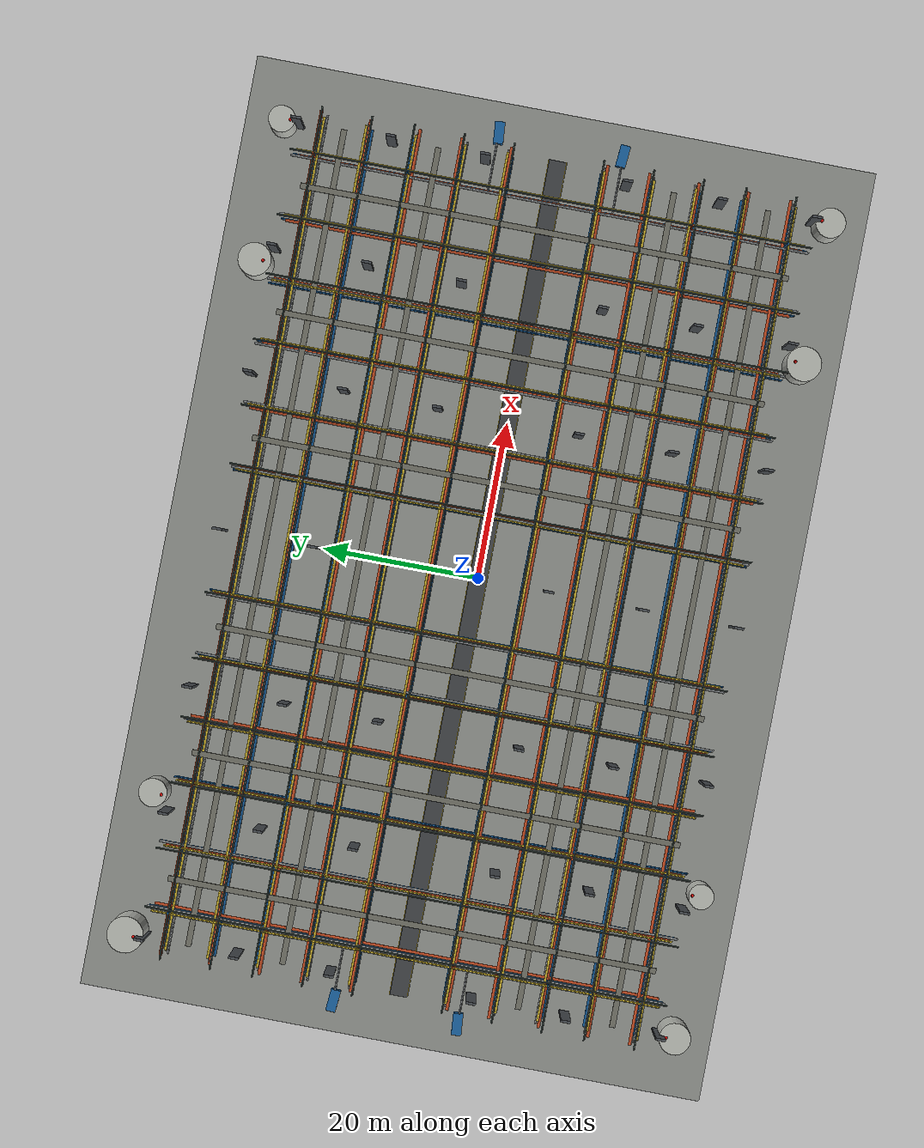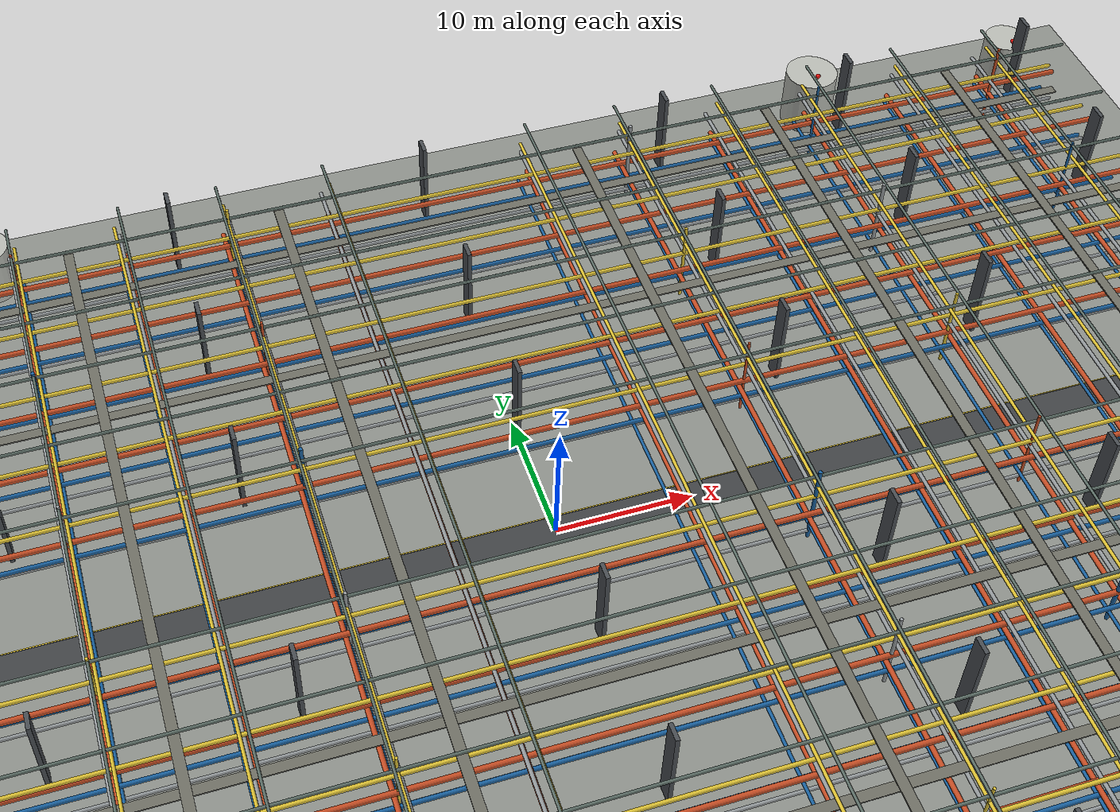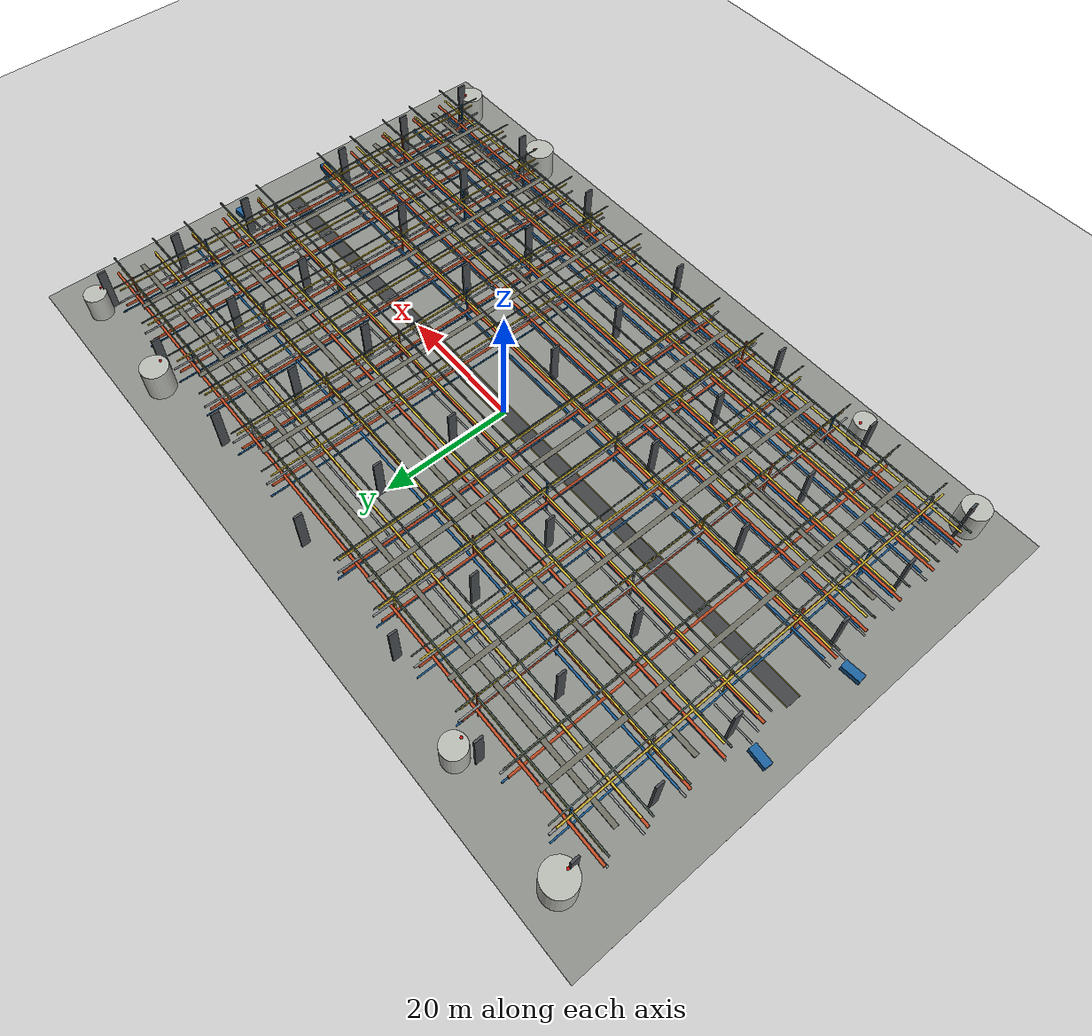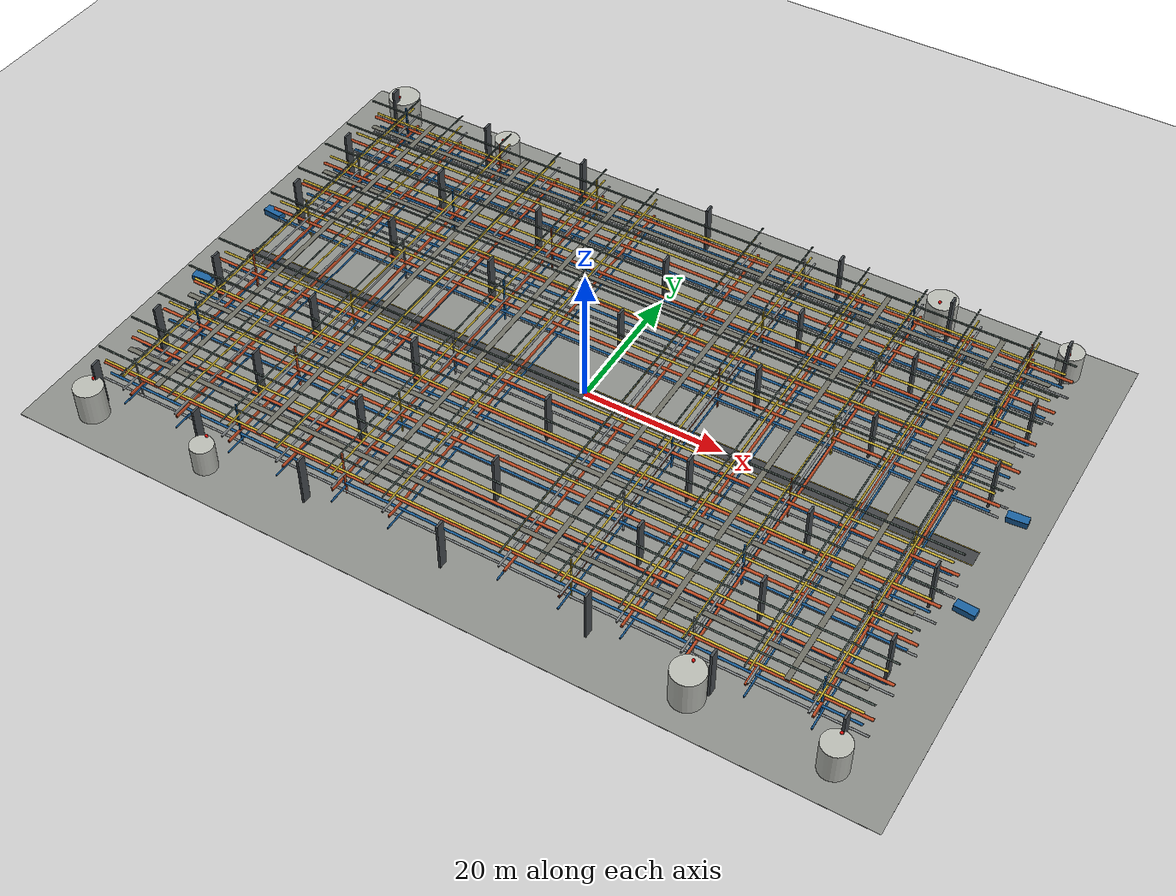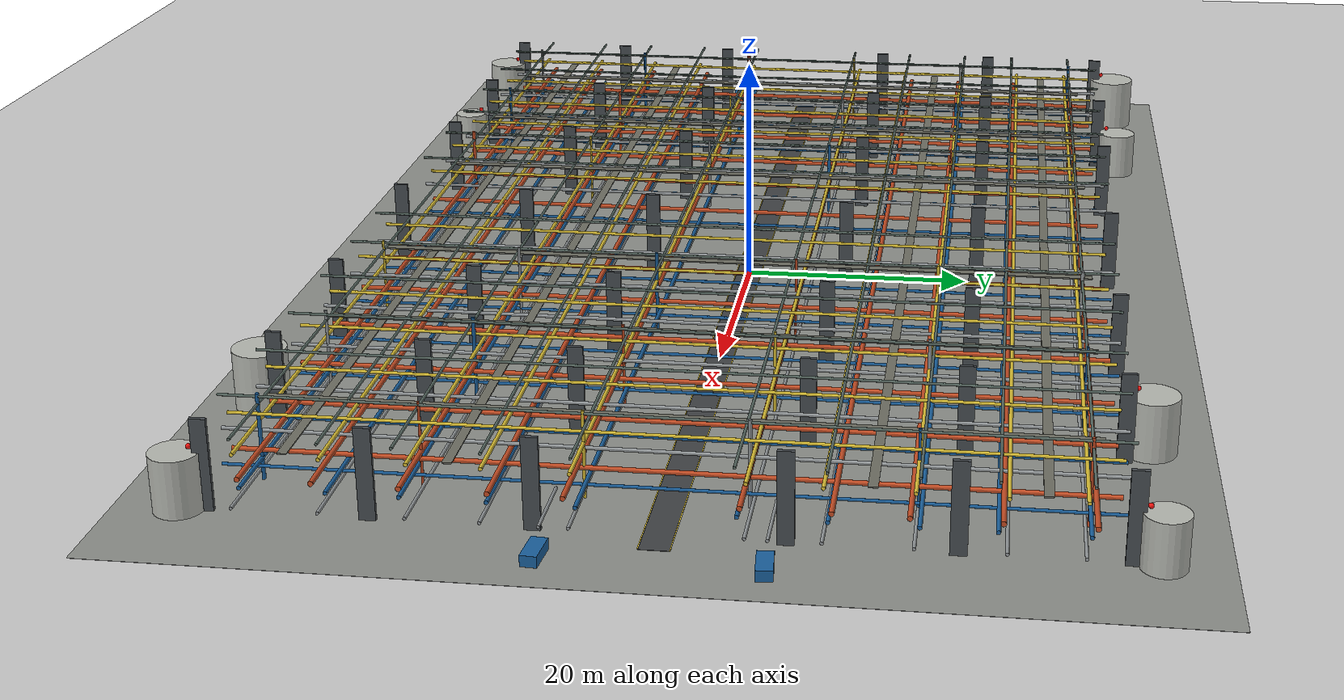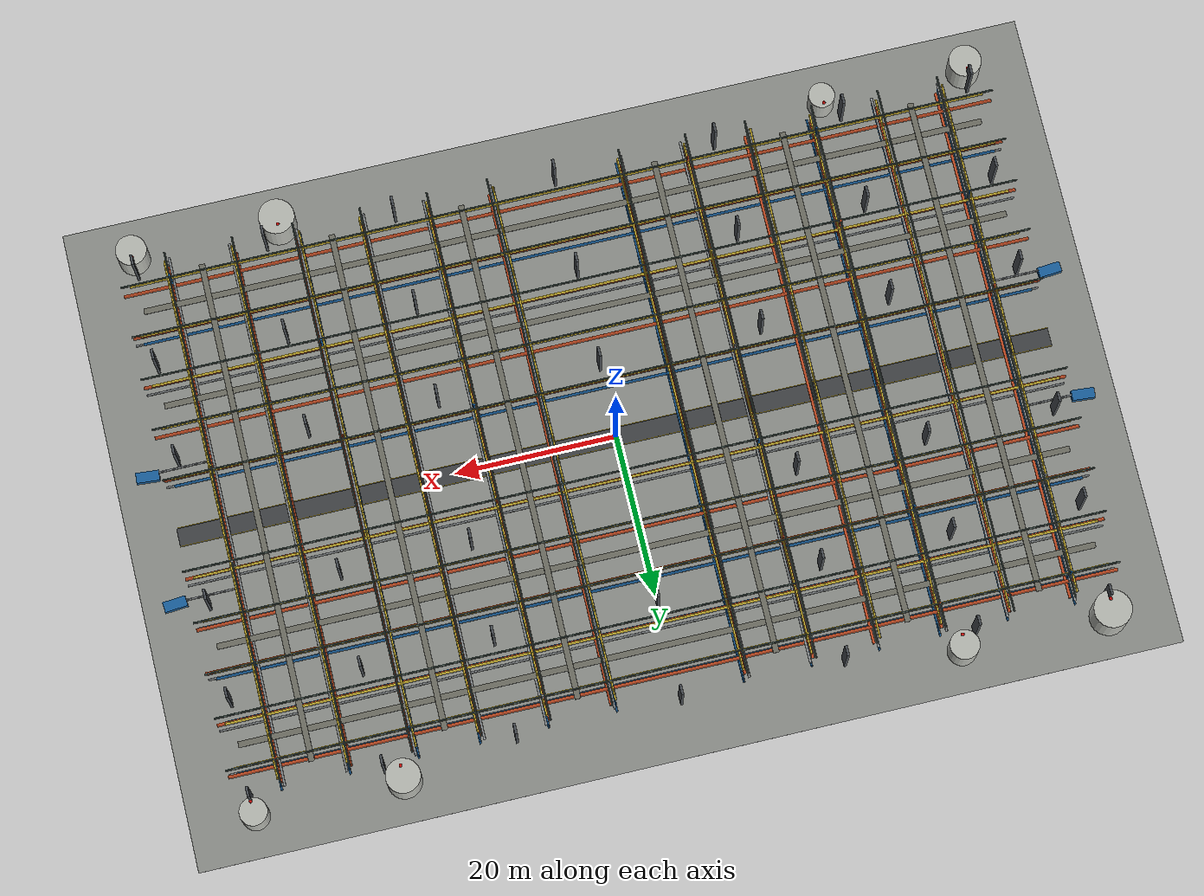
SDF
<?xml version="1.0" ?>
<sdf version="1.6">
  <world name="default">
    <scene>
      <ambient>0.82 0.84 0.86 1</ambient>
      <background>0.48 0.52 0.56 1</background>
      <shadows>true</shadows>
    </scene>

    <gui fullscreen="0">
      <camera name="user_camera">
        <pose>-48 -56 30 0 0.44 0.78</pose>
      </camera>
    </gui>

    <include><uri>model://sun</uri></include>
    <include><uri>model://ground_plane</uri></include>

    <physics name="default_physics" default="0" type="ode">
      <gravity>0 0 -9.8066</gravity>
      <ode>
        <solver><type>quick</type><iters>10</iters><sor>1.3</sor><use_dynamic_moi_rescaling>0</use_dynamic_moi_rescaling></solver>
        <constraints><cfm>0</cfm><erp>0.2</erp><contact_max_correcting_vel>100</contact_max_correcting_vel><contact_surface_layer>0.001</contact_surface_layer></constraints>
      </ode>
      <max_step_size>0.004</max_step_size>
      <real_time_factor>1</real_time_factor>
      <real_time_update_rate>250</real_time_update_rate>
      <magnetic_field>6.0e-6 2.3e-5 -4.2e-5</magnetic_field>
    </physics>

    <model name="pipe_factory_floor">
      <static>true</static>
      <link name="concrete_pad">
        <pose>0 0 0.01 0 0 0</pose>
        <collision name="collision">
          <geometry><box><size>120 80 0.02</size></box></geometry>
        </collision>
        <visual name="visual">
          <geometry><box><size>120 80 0.02</size></box></geometry>
          <material>
            <ambient>0.42 0.43 0.42 1</ambient>
            <diffuse>0.55 0.56 0.54 1</diffuse>
          </material>
        </visual>
      </link>
      <link name="center_safety_lane">
        <pose>0 0 0.035 0 0 0</pose>
        <visual name="visual">
          <geometry><box><size>108 2.2 0.03</size></box></geometry>
          <material>
            <ambient>0.16 0.17 0.18 1</ambient>
            <diffuse>0.25 0.26 0.27 1</diffuse>
          </material>
        </visual>
      </link>
      <link name="north_lane_line">
        <pose>0 1.15 0.055 0 0 0</pose>
        <visual name="visual">
          <geometry><box><size>108 0.08 0.02</size></box></geometry>
          <material>
            <ambient>0.48 0.42 0.12 1</ambient>
            <diffuse>0.86 0.75 0.20 1</diffuse>
          </material>
        </visual>
      </link>
      <link name="south_lane_line">
        <pose>0 -1.15 0.055 0 0 0</pose>
        <visual name="visual">
          <geometry><box><size>108 0.08 0.02</size></box></geometry>
          <material>
            <ambient>0.48 0.42 0.12 1</ambient>
            <diffuse>0.86 0.75 0.20 1</diffuse>
          </material>
        </visual>
      </link>
    </model>

    <model name="dense_interwoven_pipe_grid">
      <static>true</static>
      <link name="x_pipe_r00_l0">
        <pose>0 -30.32 1.35 0 1.5708 0</pose>
        <collision name="collision">
          <geometry><cylinder><radius>0.130</radius><length>108.00</length></cylinder></geometry>
        </collision>
        <visual name="visual">
          <geometry><cylinder><radius>0.130</radius><length>108.00</length></cylinder></geometry>
          <material>
            <ambient>0.34 0.35 0.36 1</ambient>
            <diffuse>0.58 0.60 0.61 1</diffuse>
          </material>
        </visual>
      </link>
      <link name="x_pipe_r00_l1">
        <pose>0 -30.00 2.45 0 1.5708 0</pose>
        <collision name="collision">
          <geometry><cylinder><radius>0.160</radius><length>106.00</length></cylinder></geometry>
        </collision>
        <visual name="visual">
          <geometry><cylinder><radius>0.160</radius><length>106.00</length></cylinder></geometry>
          <material>
            <ambient>0.05 0.22 0.36 1</ambient>
            <diffuse>0.10 0.38 0.62 1</diffuse>
          </material>
        </visual>
      </link>
      <link name="x_pipe_r00_l2">
        <pose>0 -29.68 3.65 0 1.5708 0</pose>
        <collision name="collision">
          <geometry><cylinder><radius>0.200</radius><length>108.00</length></cylinder></geometry>
        </collision>
        <visual name="visual">
          <geometry><cylinder><radius>0.200</radius><length>108.00</length></cylinder></geometry>
          <material>
            <ambient>0.45 0.17 0.08 1</ambient>
            <diffuse>0.77 0.30 0.14 1</diffuse>
          </material>
        </visual>
      </link>
      <link name="x_pipe_r00_l3">
        <pose>0 -30.32 5.05 0 1.5708 0</pose>
        <collision name="collision">
          <geometry><cylinder><radius>0.150</radius><length>106.00</length></cylinder></geometry>
        </collision>
        <visual name="visual">
          <geometry><cylinder><radius>0.150</radius><length>106.00</length></cylinder></geometry>
          <material>
            <ambient>0.48 0.42 0.12 1</ambient>
            <diffuse>0.86 0.75 0.20 1</diffuse>
          </material>
        </visual>
      </link>
      <link name="x_pipe_r00_l4">
        <pose>0 -30.00 6.75 0 1.5708 0</pose>
        <collision name="collision">
          <geometry><cylinder><radius>0.110</radius><length>108.00</length></cylinder></geometry>
        </collision>
        <visual name="visual">
          <geometry><cylinder><radius>0.110</radius><length>108.00</length></cylinder></geometry>
          <material>
            <ambient>0.20 0.24 0.23 1</ambient>
            <diffuse>0.36 0.43 0.40 1</diffuse>
          </material>
        </visual>
      </link>
      <link name="x_pipe_r01_l0">
        <pose>0 -24.00 1.35 0 1.5708 0</pose>
        <collision name="collision">
          <geometry><cylinder><radius>0.130</radius><length>108.00</length></cylinder></geometry>
        </collision>
        <visual name="visual">
          <geometry><cylinder><radius>0.130</radius><length>108.00</length></cylinder></geometry>
          <material>
            <ambient>0.34 0.35 0.36 1</ambient>
            <diffuse>0.58 0.60 0.61 1</diffuse>
          </material>
        </visual>
      </link>
      <link name="x_pipe_r01_l1">
        <pose>0 -23.68 2.45 0 1.5708 0</pose>
        <collision name="collision">
          <geometry><cylinder><radius>0.160</radius><length>106.00</length></cylinder></geometry>
        </collision>
        <visual name="visual">
          <geometry><cylinder><radius>0.160</radius><length>106.00</length></cylinder></geometry>
          <material>
            <ambient>0.05 0.22 0.36 1</ambient>
            <diffuse>0.10 0.38 0.62 1</diffuse>
          </material>
        </visual>
      </link>
      <link name="x_pipe_r01_l2">
        <pose>0 -24.32 3.65 0 1.5708 0</pose>
        <collision name="collision">
          <geometry><cylinder><radius>0.200</radius><length>108.00</length></cylinder></geometry>
        </collision>
        <visual name="visual">
          <geometry><cylinder><radius>0.200</radius><length>108.00</length></cylinder></geometry>
          <material>
            <ambient>0.45 0.17 0.08 1</ambient>
            <diffuse>0.77 0.30 0.14 1</diffuse>
          </material>
        </visual>
      </link>
      <link name="x_pipe_r01_l3">
        <pose>0 -24.00 5.05 0 1.5708 0</pose>
        <collision name="collision">
          <geometry><cylinder><radius>0.150</radius><length>106.00</length></cylinder></geometry>
        </collision>
        <visual name="visual">
          <geometry><cylinder><radius>0.150</radius><length>106.00</length></cylinder></geometry>
          <material>
            <ambient>0.48 0.42 0.12 1</ambient>
            <diffuse>0.86 0.75 0.20 1</diffuse>
          </material>
        </visual>
      </link>
      <link name="x_pipe_r01_l4">
        <pose>0 -23.68 6.75 0 1.5708 0</pose>
        <collision name="collision">
          <geometry><cylinder><radius>0.110</radius><length>108.00</length></cylinder></geometry>
        </collision>
        <visual name="visual">
          <geometry><cylinder><radius>0.110</radius><length>108.00</length></cylinder></geometry>
          <material>
            <ambient>0.20 0.24 0.23 1</ambient>
            <diffuse>0.36 0.43 0.40 1</diffuse>
          </material>
        </visual>
      </link>
      <link name="x_pipe_r02_l0">
        <pose>0 -17.68 1.35 0 1.5708 0</pose>
        <collision name="collision">
          <geometry><cylinder><radius>0.130</radius><length>108.00</length></cylinder></geometry>
        </collision>
        <visual name="visual">
          <geometry><cylinder><radius>0.130</radius><length>108.00</length></cylinder></geometry>
          <material>
            <ambient>0.34 0.35 0.36 1</ambient>
            <diffuse>0.58 0.60 0.61 1</diffuse>
          </material>
        </visual>
      </link>
      <link name="x_pipe_r02_l1">
        <pose>0 -18.32 2.45 0 1.5708 0</pose>
        <collision name="collision">
          <geometry><cylinder><radius>0.160</radius><length>106.00</length></cylinder></geometry>
        </collision>
        <visual name="visual">
          <geometry><cylinder><radius>0.160</radius><length>106.00</length></cylinder></geometry>
          <material>
            <ambient>0.05 0.22 0.36 1</ambient>
            <diffuse>0.10 0.38 0.62 1</diffuse>
          </material>
        </visual>
      </link>
      <link name="x_pipe_r02_l2">
        <pose>0 -18.00 3.65 0 1.5708 0</pose>
        <collision name="collision">
          <geometry><cylinder><radius>0.200</radius><length>108.00</length></cylinder></geometry>
        </collision>
        <visual name="visual">
          <geometry><cylinder><radius>0.200</radius><length>108.00</length></cylinder></geometry>
          <material>
            <ambient>0.45 0.17 0.08 1</ambient>
            <diffuse>0.77 0.30 0.14 1</diffuse>
          </material>
        </visual>
      </link>
      <link name="x_pipe_r02_l3">
        <pose>0 -17.68 5.05 0 1.5708 0</pose>
        <collision name="collision">
          <geometry><cylinder><radius>0.150</radius><length>106.00</length></cylinder></geometry>
        </collision>
        <visual name="visual">
          <geometry><cylinder><radius>0.150</radius><length>106.00</length></cylinder></geometry>
          <material>
            <ambient>0.48 0.42 0.12 1</ambient>
            <diffuse>0.86 0.75 0.20 1</diffuse>
          </material>
        </visual>
      </link>
      <link name="x_pipe_r02_l4">
        <pose>0 -18.32 6.75 0 1.5708 0</pose>
        <collision name="collision">
          <geometry><cylinder><radius>0.110</radius><length>108.00</length></cylinder></geometry>
        </collision>
        <visual name="visual">
          <geometry><cylinder><radius>0.110</radius><length>108.00</length></cylinder></geometry>
          <material>
            <ambient>0.20 0.24 0.23 1</ambient>
            <diffuse>0.36 0.43 0.40 1</diffuse>
          </material>
        </visual>
      </link>
      <link name="x_pipe_r03_l0">
        <pose>0 -12.32 1.35 0 1.5708 0</pose>
        <collision name="collision">
          <geometry><cylinder><radius>0.130</radius><length>108.00</length></cylinder></geometry>
        </collision>
        <visual name="visual">
          <geometry><cylinder><radius>0.130</radius><length>108.00</length></cylinder></geometry>
          <material>
            <ambient>0.34 0.35 0.36 1</ambient>
            <diffuse>0.58 0.60 0.61 1</diffuse>
          </material>
        </visual>
      </link>
      <link name="x_pipe_r03_l1">
        <pose>0 -12.00 2.45 0 1.5708 0</pose>
        <collision name="collision">
          <geometry><cylinder><radius>0.160</radius><length>106.00</length></cylinder></geometry>
        </collision>
        <visual name="visual">
          <geometry><cylinder><radius>0.160</radius><length>106.00</length></cylinder></geometry>
          <material>
            <ambient>0.05 0.22 0.36 1</ambient>
            <diffuse>0.10 0.38 0.62 1</diffuse>
          </material>
        </visual>
      </link>
      <link name="x_pipe_r03_l2">
        <pose>0 -11.68 3.65 0 1.5708 0</pose>
        <collision name="collision">
          <geometry><cylinder><radius>0.200</radius><length>108.00</length></cylinder></geometry>
        </collision>
        <visual name="visual">
          <geometry><cylinder><radius>0.200</radius><length>108.00</length></cylinder></geometry>
          <material>
            <ambient>0.45 0.17 0.08 1</ambient>
            <diffuse>0.77 0.30 0.14 1</diffuse>
          </material>
        </visual>
      </link>
      <link name="x_pipe_r03_l3">
        <pose>0 -12.32 5.05 0 1.5708 0</pose>
        <collision name="collision">
          <geometry><cylinder><radius>0.150</radius><length>106.00</length></cylinder></geometry>
        </collision>
        <visual name="visual">
          <geometry><cylinder><radius>0.150</radius><length>106.00</length></cylinder></geometry>
          <material>
            <ambient>0.48 0.42 0.12 1</ambient>
            <diffuse>0.86 0.75 0.20 1</diffuse>
          </material>
        </visual>
      </link>
      <link name="x_pipe_r03_l4">
        <pose>0 -12.00 6.75 0 1.5708 0</pose>
        <collision name="collision">
          <geometry><cylinder><radius>0.110</radius><length>108.00</length></cylinder></geometry>
        </collision>
        <visual name="visual">
          <geometry><cylinder><radius>0.110</radius><length>108.00</length></cylinder></geometry>
          <material>
            <ambient>0.20 0.24 0.23 1</ambient>
            <diffuse>0.36 0.43 0.40 1</diffuse>
          </material>
        </visual>
      </link>
      <link name="x_pipe_r04_l0">
        <pose>0 -6.00 1.35 0 1.5708 0</pose>
        <collision name="collision">
          <geometry><cylinder><radius>0.130</radius><length>108.00</length></cylinder></geometry>
        </collision>
        <visual name="visual">
          <geometry><cylinder><radius>0.130</radius><length>108.00</length></cylinder></geometry>
          <material>
            <ambient>0.34 0.35 0.36 1</ambient>
            <diffuse>0.58 0.60 0.61 1</diffuse>
          </material>
        </visual>
      </link>
      <link name="x_pipe_r04_l1">
        <pose>0 -5.68 2.45 0 1.5708 0</pose>
        <collision name="collision">
          <geometry><cylinder><radius>0.160</radius><length>106.00</length></cylinder></geometry>
        </collision>
        <visual name="visual">
          <geometry><cylinder><radius>0.160</radius><length>106.00</length></cylinder></geometry>
          <material>
            <ambient>0.05 0.22 0.36 1</ambient>
            <diffuse>0.10 0.38 0.62 1</diffuse>
          </material>
        </visual>
      </link>
      <link name="x_pipe_r04_l2">
        <pose>0 -6.32 3.65 0 1.5708 0</pose>
        <collision name="collision">
          <geometry><cylinder><radius>0.200</radius><length>108.00</length></cylinder></geometry>
        </collision>
        <visual name="visual">
          <geometry><cylinder><radius>0.200</radius><length>108.00</length></cylinder></geometry>
          <material>
            <ambient>0.45 0.17 0.08 1</ambient>
            <diffuse>0.77 0.30 0.14 1</diffuse>
          </material>
        </visual>
      </link>
      <link name="x_pipe_r04_l3">
        <pose>0 -6.00 5.05 0 1.5708 0</pose>
        <collision name="collision">
          <geometry><cylinder><radius>0.150</radius><length>106.00</length></cylinder></geometry>
        </collision>
        <visual name="visual">
          <geometry><cylinder><radius>0.150</radius><length>106.00</length></cylinder></geometry>
          <material>
            <ambient>0.48 0.42 0.12 1</ambient>
            <diffuse>0.86 0.75 0.20 1</diffuse>
          </material>
        </visual>
      </link>
      <link name="x_pipe_r04_l4">
        <pose>0 -5.68 6.75 0 1.5708 0</pose>
        <collision name="collision">
          <geometry><cylinder><radius>0.110</radius><length>108.00</length></cylinder></geometry>
        </collision>
        <visual name="visual">
          <geometry><cylinder><radius>0.110</radius><length>108.00</length></cylinder></geometry>
          <material>
            <ambient>0.20 0.24 0.23 1</ambient>
            <diffuse>0.36 0.43 0.40 1</diffuse>
          </material>
        </visual>
      </link>
      <link name="x_pipe_r05_l0">
        <pose>0 6.32 1.35 0 1.5708 0</pose>
        <collision name="collision">
          <geometry><cylinder><radius>0.130</radius><length>108.00</length></cylinder></geometry>
        </collision>
        <visual name="visual">
          <geometry><cylinder><radius>0.130</radius><length>108.00</length></cylinder></geometry>
          <material>
            <ambient>0.34 0.35 0.36 1</ambient>
            <diffuse>0.58 0.60 0.61 1</diffuse>
          </material>
        </visual>
      </link>
      <link name="x_pipe_r05_l1">
        <pose>0 5.68 2.45 0 1.5708 0</pose>
        <collision name="collision">
          <geometry><cylinder><radius>0.160</radius><length>106.00</length></cylinder></geometry>
        </collision>
        <visual name="visual">
          <geometry><cylinder><radius>0.160</radius><length>106.00</length></cylinder></geometry>
          <material>
            <ambient>0.05 0.22 0.36 1</ambient>
            <diffuse>0.10 0.38 0.62 1</diffuse>
          </material>
        </visual>
      </link>
      <link name="x_pipe_r05_l2">
        <pose>0 6.00 3.65 0 1.5708 0</pose>
        <collision name="collision">
          <geometry><cylinder><radius>0.200</radius><length>108.00</length></cylinder></geometry>
        </collision>
        <visual name="visual">
          <geometry><cylinder><radius>0.200</radius><length>108.00</length></cylinder></geometry>
          <material>
            <ambient>0.45 0.17 0.08 1</ambient>
            <diffuse>0.77 0.30 0.14 1</diffuse>
          </material>
        </visual>
      </link>
      <link name="x_pipe_r05_l3">
        <pose>0 6.32 5.05 0 1.5708 0</pose>
        <collision name="collision">
          <geometry><cylinder><radius>0.150</radius><length>106.00</length></cylinder></geometry>
        </collision>
        <visual name="visual">
          <geometry><cylinder><radius>0.150</radius><length>106.00</length></cylinder></geometry>
          <material>
            <ambient>0.48 0.42 0.12 1</ambient>
            <diffuse>0.86 0.75 0.20 1</diffuse>
          </material>
        </visual>
      </link>
      <link name="x_pipe_r05_l4">
        <pose>0 5.68 6.75 0 1.5708 0</pose>
        <collision name="collision">
          <geometry><cylinder><radius>0.110</radius><length>108.00</length></cylinder></geometry>
        </collision>
        <visual name="visual">
          <geometry><cylinder><radius>0.110</radius><length>108.00</length></cylinder></geometry>
          <material>
            <ambient>0.20 0.24 0.23 1</ambient>
            <diffuse>0.36 0.43 0.40 1</diffuse>
          </material>
        </visual>
      </link>
      <link name="x_pipe_r06_l0">
        <pose>0 11.68 1.35 0 1.5708 0</pose>
        <collision name="collision">
          <geometry><cylinder><radius>0.130</radius><length>108.00</length></cylinder></geometry>
        </collision>
        <visual name="visual">
          <geometry><cylinder><radius>0.130</radius><length>108.00</length></cylinder></geometry>
          <material>
            <ambient>0.34 0.35 0.36 1</ambient>
            <diffuse>0.58 0.60 0.61 1</diffuse>
          </material>
        </visual>
      </link>
      <link name="x_pipe_r06_l1">
        <pose>0 12.00 2.45 0 1.5708 0</pose>
        <collision name="collision">
          <geometry><cylinder><radius>0.160</radius><length>106.00</length></cylinder></geometry>
        </collision>
        <visual name="visual">
          <geometry><cylinder><radius>0.160</radius><length>106.00</length></cylinder></geometry>
          <material>
            <ambient>0.05 0.22 0.36 1</ambient>
            <diffuse>0.10 0.38 0.62 1</diffuse>
          </material>
        </visual>
      </link>
      <link name="x_pipe_r06_l2">
        <pose>0 12.32 3.65 0 1.5708 0</pose>
        <collision name="collision">
          <geometry><cylinder><radius>0.200</radius><length>108.00</length></cylinder></geometry>
        </collision>
        <visual name="visual">
          <geometry><cylinder><radius>0.200</radius><length>108.00</length></cylinder></geometry>
          <material>
            <ambient>0.45 0.17 0.08 1</ambient>
            <diffuse>0.77 0.30 0.14 1</diffuse>
          </material>
        </visual>
      </link>
      <link name="x_pipe_r06_l3">
        <pose>0 11.68 5.05 0 1.5708 0</pose>
        <collision name="collision">
          <geometry><cylinder><radius>0.150</radius><length>106.00</length></cylinder></geometry>
        </collision>
        <visual name="visual">
          <geometry><cylinder><radius>0.150</radius><length>106.00</length></cylinder></geometry>
          <material>
            <ambient>0.48 0.42 0.12 1</ambient>
            <diffuse>0.86 0.75 0.20 1</diffuse>
          </material>
        </visual>
      </link>
      <link name="x_pipe_r06_l4">
        <pose>0 12.00 6.75 0 1.5708 0</pose>
        <collision name="collision">
          <geometry><cylinder><radius>0.110</radius><length>108.00</length></cylinder></geometry>
        </collision>
        <visual name="visual">
          <geometry><cylinder><radius>0.110</radius><length>108.00</length></cylinder></geometry>
          <material>
            <ambient>0.20 0.24 0.23 1</ambient>
            <diffuse>0.36 0.43 0.40 1</diffuse>
          </material>
        </visual>
      </link>
      <link name="x_pipe_r07_l0">
        <pose>0 18.00 1.35 0 1.5708 0</pose>
        <collision name="collision">
          <geometry><cylinder><radius>0.130</radius><length>108.00</length></cylinder></geometry>
        </collision>
        <visual name="visual">
          <geometry><cylinder><radius>0.130</radius><length>108.00</length></cylinder></geometry>
          <material>
            <ambient>0.34 0.35 0.36 1</ambient>
            <diffuse>0.58 0.60 0.61 1</diffuse>
          </material>
        </visual>
      </link>
      <link name="x_pipe_r07_l1">
        <pose>0 18.32 2.45 0 1.5708 0</pose>
        <collision name="collision">
          <geometry><cylinder><radius>0.160</radius><length>106.00</length></cylinder></geometry>
        </collision>
        <visual name="visual">
          <geometry><cylinder><radius>0.160</radius><length>106.00</length></cylinder></geometry>
          <material>
            <ambient>0.05 0.22 0.36 1</ambient>
            <diffuse>0.10 0.38 0.62 1</diffuse>
          </material>
        </visual>
      </link>
      <link name="x_pipe_r07_l2">
        <pose>0 17.68 3.65 0 1.5708 0</pose>
        <collision name="collision">
          <geometry><cylinder><radius>0.200</radius><length>108.00</length></cylinder></geometry>
        </collision>
        <visual name="visual">
          <geometry><cylinder><radius>0.200</radius><length>108.00</length></cylinder></geometry>
          <material>
            <ambient>0.45 0.17 0.08 1</ambient>
            <diffuse>0.77 0.30 0.14 1</diffuse>
          </material>
        </visual>
      </link>
      <link name="x_pipe_r07_l3">
        <pose>0 18.00 5.05 0 1.5708 0</pose>
        <collision name="collision">
          <geometry><cylinder><radius>0.150</radius><length>106.00</length></cylinder></geometry>
        </collision>
        <visual name="visual">
          <geometry><cylinder><radius>0.150</radius><length>106.00</length></cylinder></geometry>
          <material>
            <ambient>0.48 0.42 0.12 1</ambient>
            <diffuse>0.86 0.75 0.20 1</diffuse>
          </material>
        </visual>
      </link>
      <link name="x_pipe_r07_l4">
        <pose>0 18.32 6.75 0 1.5708 0</pose>
        <collision name="collision">
          <geometry><cylinder><radius>0.110</radius><length>108.00</length></cylinder></geometry>
        </collision>
        <visual name="visual">
          <geometry><cylinder><radius>0.110</radius><length>108.00</length></cylinder></geometry>
          <material>
            <ambient>0.20 0.24 0.23 1</ambient>
            <diffuse>0.36 0.43 0.40 1</diffuse>
          </material>
        </visual>
      </link>
      <link name="x_pipe_r08_l0">
        <pose>0 24.32 1.35 0 1.5708 0</pose>
        <collision name="collision">
          <geometry><cylinder><radius>0.130</radius><length>108.00</length></cylinder></geometry>
        </collision>
        <visual name="visual">
          <geometry><cylinder><radius>0.130</radius><length>108.00</length></cylinder></geometry>
          <material>
            <ambient>0.34 0.35 0.36 1</ambient>
            <diffuse>0.58 0.60 0.61 1</diffuse>
          </material>
        </visual>
      </link>
      <link name="x_pipe_r08_l1">
        <pose>0 23.68 2.45 0 1.5708 0</pose>
        <collision name="collision">
          <geometry><cylinder><radius>0.160</radius><length>106.00</length></cylinder></geometry>
        </collision>
        <visual name="visual">
          <geometry><cylinder><radius>0.160</radius><length>106.00</length></cylinder></geometry>
          <material>
            <ambient>0.05 0.22 0.36 1</ambient>
            <diffuse>0.10 0.38 0.62 1</diffuse>
          </material>
        </visual>
      </link>
      <link name="x_pipe_r08_l2">
        <pose>0 24.00 3.65 0 1.5708 0</pose>
        <collision name="collision">
          <geometry><cylinder><radius>0.200</radius><length>108.00</length></cylinder></geometry>
        </collision>
        <visual name="visual">
          <geometry><cylinder><radius>0.200</radius><length>108.00</length></cylinder></geometry>
          <material>
            <ambient>0.45 0.17 0.08 1</ambient>
            <diffuse>0.77 0.30 0.14 1</diffuse>
          </material>
        </visual>
      </link>
      <link name="x_pipe_r08_l3">
        <pose>0 24.32 5.05 0 1.5708 0</pose>
        <collision name="collision">
          <geometry><cylinder><radius>0.150</radius><length>106.00</length></cylinder></geometry>
        </collision>
        <visual name="visual">
          <geometry><cylinder><radius>0.150</radius><length>106.00</length></cylinder></geometry>
          <material>
            <ambient>0.48 0.42 0.12 1</ambient>
            <diffuse>0.86 0.75 0.20 1</diffuse>
          </material>
        </visual>
      </link>
      <link name="x_pipe_r08_l4">
        <pose>0 23.68 6.75 0 1.5708 0</pose>
        <collision name="collision">
          <geometry><cylinder><radius>0.110</radius><length>108.00</length></cylinder></geometry>
        </collision>
        <visual name="visual">
          <geometry><cylinder><radius>0.110</radius><length>108.00</length></cylinder></geometry>
          <material>
            <ambient>0.20 0.24 0.23 1</ambient>
            <diffuse>0.36 0.43 0.40 1</diffuse>
          </material>
        </visual>
      </link>
      <link name="x_pipe_r09_l0">
        <pose>0 29.68 1.35 0 1.5708 0</pose>
        <collision name="collision">
          <geometry><cylinder><radius>0.130</radius><length>108.00</length></cylinder></geometry>
        </collision>
        <visual name="visual">
          <geometry><cylinder><radius>0.130</radius><length>108.00</length></cylinder></geometry>
          <material>
            <ambient>0.34 0.35 0.36 1</ambient>
            <diffuse>0.58 0.60 0.61 1</diffuse>
          </material>
        </visual>
      </link>
      <link name="x_pipe_r09_l1">
        <pose>0 30.00 2.45 0 1.5708 0</pose>
        <collision name="collision">
          <geometry><cylinder><radius>0.160</radius><length>106.00</length></cylinder></geometry>
        </collision>
        <visual name="visual">
          <geometry><cylinder><radius>0.160</radius><length>106.00</length></cylinder></geometry>
          <material>
            <ambient>0.05 0.22 0.36 1</ambient>
            <diffuse>0.10 0.38 0.62 1</diffuse>
          </material>
        </visual>
      </link>
      <link name="x_pipe_r09_l2">
        <pose>0 30.32 3.65 0 1.5708 0</pose>
        <collision name="collision">
          <geometry><cylinder><radius>0.200</radius><length>108.00</length></cylinder></geometry>
        </collision>
        <visual name="visual">
          <geometry><cylinder><radius>0.200</radius><length>108.00</length></cylinder></geometry>
          <material>
            <ambient>0.45 0.17 0.08 1</ambient>
            <diffuse>0.77 0.30 0.14 1</diffuse>
          </material>
        </visual>
      </link>
      <link name="x_pipe_r09_l3">
        <pose>0 29.68 5.05 0 1.5708 0</pose>
        <collision name="collision">
          <geometry><cylinder><radius>0.150</radius><length>106.00</length></cylinder></geometry>
        </collision>
        <visual name="visual">
          <geometry><cylinder><radius>0.150</radius><length>106.00</length></cylinder></geometry>
          <material>
            <ambient>0.48 0.42 0.12 1</ambient>
            <diffuse>0.86 0.75 0.20 1</diffuse>
          </material>
        </visual>
      </link>
      <link name="x_pipe_r09_l4">
        <pose>0 30.00 6.75 0 1.5708 0</pose>
        <collision name="collision">
          <geometry><cylinder><radius>0.110</radius><length>108.00</length></cylinder></geometry>
        </collision>
        <visual name="visual">
          <geometry><cylinder><radius>0.110</radius><length>108.00</length></cylinder></geometry>
          <material>
            <ambient>0.20 0.24 0.23 1</ambient>
            <diffuse>0.36 0.43 0.40 1</diffuse>
          </material>
        </visual>
      </link>
      <link name="y_pipe_c00_l0">
        <pose>-48.28 0 1.90 1.5708 0 0</pose>
        <collision name="collision">
          <geometry><cylinder><radius>0.120</radius><length>66.00</length></cylinder></geometry>
        </collision>
        <visual name="visual">
          <geometry><cylinder><radius>0.120</radius><length>66.00</length></cylinder></geometry>
          <material>
            <ambient>0.05 0.22 0.36 1</ambient>
            <diffuse>0.10 0.38 0.62 1</diffuse>
          </material>
        </visual>
      </link>
      <link name="y_pipe_c00_l1">
        <pose>-47.72 0 3.10 1.5708 0 0</pose>
        <collision name="collision">
          <geometry><cylinder><radius>0.180</radius><length>64.50</length></cylinder></geometry>
        </collision>
        <visual name="visual">
          <geometry><cylinder><radius>0.180</radius><length>64.50</length></cylinder></geometry>
          <material>
            <ambient>0.45 0.17 0.08 1</ambient>
            <diffuse>0.77 0.30 0.14 1</diffuse>
          </material>
        </visual>
      </link>
      <link name="y_pipe_c00_l2">
        <pose>-48.00 0 4.55 1.5708 0 0</pose>
        <collision name="collision">
          <geometry><cylinder><radius>0.140</radius><length>66.00</length></cylinder></geometry>
        </collision>
        <visual name="visual">
          <geometry><cylinder><radius>0.140</radius><length>66.00</length></cylinder></geometry>
          <material>
            <ambient>0.34 0.35 0.36 1</ambient>
            <diffuse>0.58 0.60 0.61 1</diffuse>
          </material>
        </visual>
      </link>
      <link name="y_pipe_c00_l3">
        <pose>-48.28 0 6.10 1.5708 0 0</pose>
        <collision name="collision">
          <geometry><cylinder><radius>0.120</radius><length>64.50</length></cylinder></geometry>
        </collision>
        <visual name="visual">
          <geometry><cylinder><radius>0.120</radius><length>64.50</length></cylinder></geometry>
          <material>
            <ambient>0.48 0.42 0.12 1</ambient>
            <diffuse>0.86 0.75 0.20 1</diffuse>
          </material>
        </visual>
      </link>
      <link name="y_pipe_c00_l4">
        <pose>-47.72 0 7.35 1.5708 0 0</pose>
        <collision name="collision">
          <geometry><cylinder><radius>0.100</radius><length>66.00</length></cylinder></geometry>
        </collision>
        <visual name="visual">
          <geometry><cylinder><radius>0.100</radius><length>66.00</length></cylinder></geometry>
          <material>
            <ambient>0.20 0.24 0.23 1</ambient>
            <diffuse>0.36 0.43 0.40 1</diffuse>
          </material>
        </visual>
      </link>
      <link name="y_pipe_c01_l0">
        <pose>-40.00 0 1.90 1.5708 0 0</pose>
        <collision name="collision">
          <geometry><cylinder><radius>0.120</radius><length>66.00</length></cylinder></geometry>
        </collision>
        <visual name="visual">
          <geometry><cylinder><radius>0.120</radius><length>66.00</length></cylinder></geometry>
          <material>
            <ambient>0.05 0.22 0.36 1</ambient>
            <diffuse>0.10 0.38 0.62 1</diffuse>
          </material>
        </visual>
      </link>
      <link name="y_pipe_c01_l1">
        <pose>-40.28 0 3.10 1.5708 0 0</pose>
        <collision name="collision">
          <geometry><cylinder><radius>0.180</radius><length>64.50</length></cylinder></geometry>
        </collision>
        <visual name="visual">
          <geometry><cylinder><radius>0.180</radius><length>64.50</length></cylinder></geometry>
          <material>
            <ambient>0.45 0.17 0.08 1</ambient>
            <diffuse>0.77 0.30 0.14 1</diffuse>
          </material>
        </visual>
      </link>
      <link name="y_pipe_c01_l2">
        <pose>-39.72 0 4.55 1.5708 0 0</pose>
        <collision name="collision">
          <geometry><cylinder><radius>0.140</radius><length>66.00</length></cylinder></geometry>
        </collision>
        <visual name="visual">
          <geometry><cylinder><radius>0.140</radius><length>66.00</length></cylinder></geometry>
          <material>
            <ambient>0.34 0.35 0.36 1</ambient>
            <diffuse>0.58 0.60 0.61 1</diffuse>
          </material>
        </visual>
      </link>
      <link name="y_pipe_c01_l3">
        <pose>-40.00 0 6.10 1.5708 0 0</pose>
        <collision name="collision">
          <geometry><cylinder><radius>0.120</radius><length>64.50</length></cylinder></geometry>
        </collision>
        <visual name="visual">
          <geometry><cylinder><radius>0.120</radius><length>64.50</length></cylinder></geometry>
          <material>
            <ambient>0.48 0.42 0.12 1</ambient>
            <diffuse>0.86 0.75 0.20 1</diffuse>
          </material>
        </visual>
      </link>
      <link name="y_pipe_c01_l4">
        <pose>-40.28 0 7.35 1.5708 0 0</pose>
        <collision name="collision">
          <geometry><cylinder><radius>0.100</radius><length>66.00</length></cylinder></geometry>
        </collision>
        <visual name="visual">
          <geometry><cylinder><radius>0.100</radius><length>66.00</length></cylinder></geometry>
          <material>
            <ambient>0.20 0.24 0.23 1</ambient>
            <diffuse>0.36 0.43 0.40 1</diffuse>
          </material>
        </visual>
      </link>
      <link name="y_pipe_c02_l0">
        <pose>-31.72 0 1.90 1.5708 0 0</pose>
        <collision name="collision">
          <geometry><cylinder><radius>0.120</radius><length>66.00</length></cylinder></geometry>
        </collision>
        <visual name="visual">
          <geometry><cylinder><radius>0.120</radius><length>66.00</length></cylinder></geometry>
          <material>
            <ambient>0.05 0.22 0.36 1</ambient>
            <diffuse>0.10 0.38 0.62 1</diffuse>
          </material>
        </visual>
      </link>
      <link name="y_pipe_c02_l1">
        <pose>-32.00 0 3.10 1.5708 0 0</pose>
        <collision name="collision">
          <geometry><cylinder><radius>0.180</radius><length>64.50</length></cylinder></geometry>
        </collision>
        <visual name="visual">
          <geometry><cylinder><radius>0.180</radius><length>64.50</length></cylinder></geometry>
          <material>
            <ambient>0.45 0.17 0.08 1</ambient>
            <diffuse>0.77 0.30 0.14 1</diffuse>
          </material>
        </visual>
      </link>
      <link name="y_pipe_c02_l2">
        <pose>-32.28 0 4.55 1.5708 0 0</pose>
        <collision name="collision">
          <geometry><cylinder><radius>0.140</radius><length>66.00</length></cylinder></geometry>
        </collision>
        <visual name="visual">
          <geometry><cylinder><radius>0.140</radius><length>66.00</length></cylinder></geometry>
          <material>
            <ambient>0.34 0.35 0.36 1</ambient>
            <diffuse>0.58 0.60 0.61 1</diffuse>
          </material>
        </visual>
      </link>
      <link name="y_pipe_c02_l3">
        <pose>-31.72 0 6.10 1.5708 0 0</pose>
        <collision name="collision">
          <geometry><cylinder><radius>0.120</radius><length>64.50</length></cylinder></geometry>
        </collision>
        <visual name="visual">
          <geometry><cylinder><radius>0.120</radius><length>64.50</length></cylinder></geometry>
          <material>
            <ambient>0.48 0.42 0.12 1</ambient>
            <diffuse>0.86 0.75 0.20 1</diffuse>
          </material>
        </visual>
      </link>
      <link name="y_pipe_c02_l4">
        <pose>-32.00 0 7.35 1.5708 0 0</pose>
        <collision name="collision">
          <geometry><cylinder><radius>0.100</radius><length>66.00</length></cylinder></geometry>
        </collision>
        <visual name="visual">
          <geometry><cylinder><radius>0.100</radius><length>66.00</length></cylinder></geometry>
          <material>
            <ambient>0.20 0.24 0.23 1</ambient>
            <diffuse>0.36 0.43 0.40 1</diffuse>
          </material>
        </visual>
      </link>
      <link name="y_pipe_c03_l0">
        <pose>-24.28 0 1.90 1.5708 0 0</pose>
        <collision name="collision">
          <geometry><cylinder><radius>0.120</radius><length>66.00</length></cylinder></geometry>
        </collision>
        <visual name="visual">
          <geometry><cylinder><radius>0.120</radius><length>66.00</length></cylinder></geometry>
          <material>
            <ambient>0.05 0.22 0.36 1</ambient>
            <diffuse>0.10 0.38 0.62 1</diffuse>
          </material>
        </visual>
      </link>
      <link name="y_pipe_c03_l1">
        <pose>-23.72 0 3.10 1.5708 0 0</pose>
        <collision name="collision">
          <geometry><cylinder><radius>0.180</radius><length>64.50</length></cylinder></geometry>
        </collision>
        <visual name="visual">
          <geometry><cylinder><radius>0.180</radius><length>64.50</length></cylinder></geometry>
          <material>
            <ambient>0.45 0.17 0.08 1</ambient>
            <diffuse>0.77 0.30 0.14 1</diffuse>
          </material>
        </visual>
      </link>
      <link name="y_pipe_c03_l2">
        <pose>-24.00 0 4.55 1.5708 0 0</pose>
        <collision name="collision">
          <geometry><cylinder><radius>0.140</radius><length>66.00</length></cylinder></geometry>
        </collision>
        <visual name="visual">
          <geometry><cylinder><radius>0.140</radius><length>66.00</length></cylinder></geometry>
          <material>
            <ambient>0.34 0.35 0.36 1</ambient>
            <diffuse>0.58 0.60 0.61 1</diffuse>
          </material>
        </visual>
      </link>
      <link name="y_pipe_c03_l3">
        <pose>-24.28 0 6.10 1.5708 0 0</pose>
        <collision name="collision">
          <geometry><cylinder><radius>0.120</radius><length>64.50</length></cylinder></geometry>
        </collision>
        <visual name="visual">
          <geometry><cylinder><radius>0.120</radius><length>64.50</length></cylinder></geometry>
          <material>
            <ambient>0.48 0.42 0.12 1</ambient>
            <diffuse>0.86 0.75 0.20 1</diffuse>
          </material>
        </visual>
      </link>
      <link name="y_pipe_c03_l4">
        <pose>-23.72 0 7.35 1.5708 0 0</pose>
        <collision name="collision">
          <geometry><cylinder><radius>0.100</radius><length>66.00</length></cylinder></geometry>
        </collision>
        <visual name="visual">
          <geometry><cylinder><radius>0.100</radius><length>66.00</length></cylinder></geometry>
          <material>
            <ambient>0.20 0.24 0.23 1</ambient>
            <diffuse>0.36 0.43 0.40 1</diffuse>
          </material>
        </visual>
      </link>
      <link name="y_pipe_c04_l0">
        <pose>-16.00 0 1.90 1.5708 0 0</pose>
        <collision name="collision">
          <geometry><cylinder><radius>0.120</radius><length>66.00</length></cylinder></geometry>
        </collision>
        <visual name="visual">
          <geometry><cylinder><radius>0.120</radius><length>66.00</length></cylinder></geometry>
          <material>
            <ambient>0.05 0.22 0.36 1</ambient>
            <diffuse>0.10 0.38 0.62 1</diffuse>
          </material>
        </visual>
      </link>
      <link name="y_pipe_c04_l1">
        <pose>-16.28 0 3.10 1.5708 0 0</pose>
        <collision name="collision">
          <geometry><cylinder><radius>0.180</radius><length>64.50</length></cylinder></geometry>
        </collision>
        <visual name="visual">
          <geometry><cylinder><radius>0.180</radius><length>64.50</length></cylinder></geometry>
          <material>
            <ambient>0.45 0.17 0.08 1</ambient>
            <diffuse>0.77 0.30 0.14 1</diffuse>
          </material>
        </visual>
      </link>
      <link name="y_pipe_c04_l2">
        <pose>-15.72 0 4.55 1.5708 0 0</pose>
        <collision name="collision">
          <geometry><cylinder><radius>0.140</radius><length>66.00</length></cylinder></geometry>
        </collision>
        <visual name="visual">
          <geometry><cylinder><radius>0.140</radius><length>66.00</length></cylinder></geometry>
          <material>
            <ambient>0.34 0.35 0.36 1</ambient>
            <diffuse>0.58 0.60 0.61 1</diffuse>
          </material>
        </visual>
      </link>
      <link name="y_pipe_c04_l3">
        <pose>-16.00 0 6.10 1.5708 0 0</pose>
        <collision name="collision">
          <geometry><cylinder><radius>0.120</radius><length>64.50</length></cylinder></geometry>
        </collision>
        <visual name="visual">
          <geometry><cylinder><radius>0.120</radius><length>64.50</length></cylinder></geometry>
          <material>
            <ambient>0.48 0.42 0.12 1</ambient>
            <diffuse>0.86 0.75 0.20 1</diffuse>
          </material>
        </visual>
      </link>
      <link name="y_pipe_c04_l4">
        <pose>-16.28 0 7.35 1.5708 0 0</pose>
        <collision name="collision">
          <geometry><cylinder><radius>0.100</radius><length>66.00</length></cylinder></geometry>
        </collision>
        <visual name="visual">
          <geometry><cylinder><radius>0.100</radius><length>66.00</length></cylinder></geometry>
          <material>
            <ambient>0.20 0.24 0.23 1</ambient>
            <diffuse>0.36 0.43 0.40 1</diffuse>
          </material>
        </visual>
      </link>
      <link name="y_pipe_c05_l0">
        <pose>-7.72 0 1.90 1.5708 0 0</pose>
        <collision name="collision">
          <geometry><cylinder><radius>0.120</radius><length>66.00</length></cylinder></geometry>
        </collision>
        <visual name="visual">
          <geometry><cylinder><radius>0.120</radius><length>66.00</length></cylinder></geometry>
          <material>
            <ambient>0.05 0.22 0.36 1</ambient>
            <diffuse>0.10 0.38 0.62 1</diffuse>
          </material>
        </visual>
      </link>
      <link name="y_pipe_c05_l1">
        <pose>-8.00 0 3.10 1.5708 0 0</pose>
        <collision name="collision">
          <geometry><cylinder><radius>0.180</radius><length>64.50</length></cylinder></geometry>
        </collision>
        <visual name="visual">
          <geometry><cylinder><radius>0.180</radius><length>64.50</length></cylinder></geometry>
          <material>
            <ambient>0.45 0.17 0.08 1</ambient>
            <diffuse>0.77 0.30 0.14 1</diffuse>
          </material>
        </visual>
      </link>
      <link name="y_pipe_c05_l2">
        <pose>-8.28 0 4.55 1.5708 0 0</pose>
        <collision name="collision">
          <geometry><cylinder><radius>0.140</radius><length>66.00</length></cylinder></geometry>
        </collision>
        <visual name="visual">
          <geometry><cylinder><radius>0.140</radius><length>66.00</length></cylinder></geometry>
          <material>
            <ambient>0.34 0.35 0.36 1</ambient>
            <diffuse>0.58 0.60 0.61 1</diffuse>
          </material>
        </visual>
      </link>
      <link name="y_pipe_c05_l3">
        <pose>-7.72 0 6.10 1.5708 0 0</pose>
        <collision name="collision">
          <geometry><cylinder><radius>0.120</radius><length>64.50</length></cylinder></geometry>
        </collision>
        <visual name="visual">
          <geometry><cylinder><radius>0.120</radius><length>64.50</length></cylinder></geometry>
          <material>
            <ambient>0.48 0.42 0.12 1</ambient>
            <diffuse>0.86 0.75 0.20 1</diffuse>
          </material>
        </visual>
      </link>
      <link name="y_pipe_c05_l4">
        <pose>-8.00 0 7.35 1.5708 0 0</pose>
        <collision name="collision">
          <geometry><cylinder><radius>0.100</radius><length>66.00</length></cylinder></geometry>
        </collision>
        <visual name="visual">
          <geometry><cylinder><radius>0.100</radius><length>66.00</length></cylinder></geometry>
          <material>
            <ambient>0.20 0.24 0.23 1</ambient>
            <diffuse>0.36 0.43 0.40 1</diffuse>
          </material>
        </visual>
      </link>
      <link name="y_pipe_c06_l0">
        <pose>7.72 0 1.90 1.5708 0 0</pose>
        <collision name="collision">
          <geometry><cylinder><radius>0.120</radius><length>66.00</length></cylinder></geometry>
        </collision>
        <visual name="visual">
          <geometry><cylinder><radius>0.120</radius><length>66.00</length></cylinder></geometry>
          <material>
            <ambient>0.05 0.22 0.36 1</ambient>
            <diffuse>0.10 0.38 0.62 1</diffuse>
          </material>
        </visual>
      </link>
      <link name="y_pipe_c06_l1">
        <pose>8.28 0 3.10 1.5708 0 0</pose>
        <collision name="collision">
          <geometry><cylinder><radius>0.180</radius><length>64.50</length></cylinder></geometry>
        </collision>
        <visual name="visual">
          <geometry><cylinder><radius>0.180</radius><length>64.50</length></cylinder></geometry>
          <material>
            <ambient>0.45 0.17 0.08 1</ambient>
            <diffuse>0.77 0.30 0.14 1</diffuse>
          </material>
        </visual>
      </link>
      <link name="y_pipe_c06_l2">
        <pose>8.00 0 4.55 1.5708 0 0</pose>
        <collision name="collision">
          <geometry><cylinder><radius>0.140</radius><length>66.00</length></cylinder></geometry>
        </collision>
        <visual name="visual">
          <geometry><cylinder><radius>0.140</radius><length>66.00</length></cylinder></geometry>
          <material>
            <ambient>0.34 0.35 0.36 1</ambient>
            <diffuse>0.58 0.60 0.61 1</diffuse>
          </material>
        </visual>
      </link>
      <link name="y_pipe_c06_l3">
        <pose>7.72 0 6.10 1.5708 0 0</pose>
        <collision name="collision">
          <geometry><cylinder><radius>0.120</radius><length>64.50</length></cylinder></geometry>
        </collision>
        <visual name="visual">
          <geometry><cylinder><radius>0.120</radius><length>64.50</length></cylinder></geometry>
          <material>
            <ambient>0.48 0.42 0.12 1</ambient>
            <diffuse>0.86 0.75 0.20 1</diffuse>
          </material>
        </visual>
      </link>
      <link name="y_pipe_c06_l4">
        <pose>8.28 0 7.35 1.5708 0 0</pose>
        <collision name="collision">
          <geometry><cylinder><radius>0.100</radius><length>66.00</length></cylinder></geometry>
        </collision>
        <visual name="visual">
          <geometry><cylinder><radius>0.100</radius><length>66.00</length></cylinder></geometry>
          <material>
            <ambient>0.20 0.24 0.23 1</ambient>
            <diffuse>0.36 0.43 0.40 1</diffuse>
          </material>
        </visual>
      </link>
      <link name="y_pipe_c07_l0">
        <pose>16.00 0 1.90 1.5708 0 0</pose>
        <collision name="collision">
          <geometry><cylinder><radius>0.120</radius><length>66.00</length></cylinder></geometry>
        </collision>
        <visual name="visual">
          <geometry><cylinder><radius>0.120</radius><length>66.00</length></cylinder></geometry>
          <material>
            <ambient>0.05 0.22 0.36 1</ambient>
            <diffuse>0.10 0.38 0.62 1</diffuse>
          </material>
        </visual>
      </link>
      <link name="y_pipe_c07_l1">
        <pose>15.72 0 3.10 1.5708 0 0</pose>
        <collision name="collision">
          <geometry><cylinder><radius>0.180</radius><length>64.50</length></cylinder></geometry>
        </collision>
        <visual name="visual">
          <geometry><cylinder><radius>0.180</radius><length>64.50</length></cylinder></geometry>
          <material>
            <ambient>0.45 0.17 0.08 1</ambient>
            <diffuse>0.77 0.30 0.14 1</diffuse>
          </material>
        </visual>
      </link>
      <link name="y_pipe_c07_l2">
        <pose>16.28 0 4.55 1.5708 0 0</pose>
        <collision name="collision">
          <geometry><cylinder><radius>0.140</radius><length>66.00</length></cylinder></geometry>
        </collision>
        <visual name="visual">
          <geometry><cylinder><radius>0.140</radius><length>66.00</length></cylinder></geometry>
          <material>
            <ambient>0.34 0.35 0.36 1</ambient>
            <diffuse>0.58 0.60 0.61 1</diffuse>
          </material>
        </visual>
      </link>
      <link name="y_pipe_c07_l3">
        <pose>16.00 0 6.10 1.5708 0 0</pose>
        <collision name="collision">
          <geometry><cylinder><radius>0.120</radius><length>64.50</length></cylinder></geometry>
        </collision>
        <visual name="visual">
          <geometry><cylinder><radius>0.120</radius><length>64.50</length></cylinder></geometry>
          <material>
            <ambient>0.48 0.42 0.12 1</ambient>
            <diffuse>0.86 0.75 0.20 1</diffuse>
          </material>
        </visual>
      </link>
      <link name="y_pipe_c07_l4">
        <pose>15.72 0 7.35 1.5708 0 0</pose>
        <collision name="collision">
          <geometry><cylinder><radius>0.100</radius><length>66.00</length></cylinder></geometry>
        </collision>
        <visual name="visual">
          <geometry><cylinder><radius>0.100</radius><length>66.00</length></cylinder></geometry>
          <material>
            <ambient>0.20 0.24 0.23 1</ambient>
            <diffuse>0.36 0.43 0.40 1</diffuse>
          </material>
        </visual>
      </link>
      <link name="y_pipe_c08_l0">
        <pose>24.28 0 1.90 1.5708 0 0</pose>
        <collision name="collision">
          <geometry><cylinder><radius>0.120</radius><length>66.00</length></cylinder></geometry>
        </collision>
        <visual name="visual">
          <geometry><cylinder><radius>0.120</radius><length>66.00</length></cylinder></geometry>
          <material>
            <ambient>0.05 0.22 0.36 1</ambient>
            <diffuse>0.10 0.38 0.62 1</diffuse>
          </material>
        </visual>
      </link>
      <link name="y_pipe_c08_l1">
        <pose>24.00 0 3.10 1.5708 0 0</pose>
        <collision name="collision">
          <geometry><cylinder><radius>0.180</radius><length>64.50</length></cylinder></geometry>
        </collision>
        <visual name="visual">
          <geometry><cylinder><radius>0.180</radius><length>64.50</length></cylinder></geometry>
          <material>
            <ambient>0.45 0.17 0.08 1</ambient>
            <diffuse>0.77 0.30 0.14 1</diffuse>
          </material>
        </visual>
      </link>
      <link name="y_pipe_c08_l2">
        <pose>23.72 0 4.55 1.5708 0 0</pose>
        <collision name="collision">
          <geometry><cylinder><radius>0.140</radius><length>66.00</length></cylinder></geometry>
        </collision>
        <visual name="visual">
          <geometry><cylinder><radius>0.140</radius><length>66.00</length></cylinder></geometry>
          <material>
            <ambient>0.34 0.35 0.36 1</ambient>
            <diffuse>0.58 0.60 0.61 1</diffuse>
          </material>
        </visual>
      </link>
      <link name="y_pipe_c08_l3">
        <pose>24.28 0 6.10 1.5708 0 0</pose>
        <collision name="collision">
          <geometry><cylinder><radius>0.120</radius><length>64.50</length></cylinder></geometry>
        </collision>
        <visual name="visual">
          <geometry><cylinder><radius>0.120</radius><length>64.50</length></cylinder></geometry>
          <material>
            <ambient>0.48 0.42 0.12 1</ambient>
            <diffuse>0.86 0.75 0.20 1</diffuse>
          </material>
        </visual>
      </link>
      <link name="y_pipe_c08_l4">
        <pose>24.00 0 7.35 1.5708 0 0</pose>
        <collision name="collision">
          <geometry><cylinder><radius>0.100</radius><length>66.00</length></cylinder></geometry>
        </collision>
        <visual name="visual">
          <geometry><cylinder><radius>0.100</radius><length>66.00</length></cylinder></geometry>
          <material>
            <ambient>0.20 0.24 0.23 1</ambient>
            <diffuse>0.36 0.43 0.40 1</diffuse>
          </material>
        </visual>
      </link>
      <link name="y_pipe_c09_l0">
        <pose>31.72 0 1.90 1.5708 0 0</pose>
        <collision name="collision">
          <geometry><cylinder><radius>0.120</radius><length>66.00</length></cylinder></geometry>
        </collision>
        <visual name="visual">
          <geometry><cylinder><radius>0.120</radius><length>66.00</length></cylinder></geometry>
          <material>
            <ambient>0.05 0.22 0.36 1</ambient>
            <diffuse>0.10 0.38 0.62 1</diffuse>
          </material>
        </visual>
      </link>
      <link name="y_pipe_c09_l1">
        <pose>32.28 0 3.10 1.5708 0 0</pose>
        <collision name="collision">
          <geometry><cylinder><radius>0.180</radius><length>64.50</length></cylinder></geometry>
        </collision>
        <visual name="visual">
          <geometry><cylinder><radius>0.180</radius><length>64.50</length></cylinder></geometry>
          <material>
            <ambient>0.45 0.17 0.08 1</ambient>
            <diffuse>0.77 0.30 0.14 1</diffuse>
          </material>
        </visual>
      </link>
      <link name="y_pipe_c09_l2">
        <pose>32.00 0 4.55 1.5708 0 0</pose>
        <collision name="collision">
          <geometry><cylinder><radius>0.140</radius><length>66.00</length></cylinder></geometry>
        </collision>
        <visual name="visual">
          <geometry><cylinder><radius>0.140</radius><length>66.00</length></cylinder></geometry>
          <material>
            <ambient>0.34 0.35 0.36 1</ambient>
            <diffuse>0.58 0.60 0.61 1</diffuse>
          </material>
        </visual>
      </link>
      <link name="y_pipe_c09_l3">
        <pose>31.72 0 6.10 1.5708 0 0</pose>
        <collision name="collision">
          <geometry><cylinder><radius>0.120</radius><length>64.50</length></cylinder></geometry>
        </collision>
        <visual name="visual">
          <geometry><cylinder><radius>0.120</radius><length>64.50</length></cylinder></geometry>
          <material>
            <ambient>0.48 0.42 0.12 1</ambient>
            <diffuse>0.86 0.75 0.20 1</diffuse>
          </material>
        </visual>
      </link>
      <link name="y_pipe_c09_l4">
        <pose>32.28 0 7.35 1.5708 0 0</pose>
        <collision name="collision">
          <geometry><cylinder><radius>0.100</radius><length>66.00</length></cylinder></geometry>
        </collision>
        <visual name="visual">
          <geometry><cylinder><radius>0.100</radius><length>66.00</length></cylinder></geometry>
          <material>
            <ambient>0.20 0.24 0.23 1</ambient>
            <diffuse>0.36 0.43 0.40 1</diffuse>
          </material>
        </visual>
      </link>
      <link name="y_pipe_c10_l0">
        <pose>40.00 0 1.90 1.5708 0 0</pose>
        <collision name="collision">
          <geometry><cylinder><radius>0.120</radius><length>66.00</length></cylinder></geometry>
        </collision>
        <visual name="visual">
          <geometry><cylinder><radius>0.120</radius><length>66.00</length></cylinder></geometry>
          <material>
            <ambient>0.05 0.22 0.36 1</ambient>
            <diffuse>0.10 0.38 0.62 1</diffuse>
          </material>
        </visual>
      </link>
      <link name="y_pipe_c10_l1">
        <pose>39.72 0 3.10 1.5708 0 0</pose>
        <collision name="collision">
          <geometry><cylinder><radius>0.180</radius><length>64.50</length></cylinder></geometry>
        </collision>
        <visual name="visual">
          <geometry><cylinder><radius>0.180</radius><length>64.50</length></cylinder></geometry>
          <material>
            <ambient>0.45 0.17 0.08 1</ambient>
            <diffuse>0.77 0.30 0.14 1</diffuse>
          </material>
        </visual>
      </link>
      <link name="y_pipe_c10_l2">
        <pose>40.28 0 4.55 1.5708 0 0</pose>
        <collision name="collision">
          <geometry><cylinder><radius>0.140</radius><length>66.00</length></cylinder></geometry>
        </collision>
        <visual name="visual">
          <geometry><cylinder><radius>0.140</radius><length>66.00</length></cylinder></geometry>
          <material>
            <ambient>0.34 0.35 0.36 1</ambient>
            <diffuse>0.58 0.60 0.61 1</diffuse>
          </material>
        </visual>
      </link>
      <link name="y_pipe_c10_l3">
        <pose>40.00 0 6.10 1.5708 0 0</pose>
        <collision name="collision">
          <geometry><cylinder><radius>0.120</radius><length>64.50</length></cylinder></geometry>
        </collision>
        <visual name="visual">
          <geometry><cylinder><radius>0.120</radius><length>64.50</length></cylinder></geometry>
          <material>
            <ambient>0.48 0.42 0.12 1</ambient>
            <diffuse>0.86 0.75 0.20 1</diffuse>
          </material>
        </visual>
      </link>
      <link name="y_pipe_c10_l4">
        <pose>39.72 0 7.35 1.5708 0 0</pose>
        <collision name="collision">
          <geometry><cylinder><radius>0.100</radius><length>66.00</length></cylinder></geometry>
        </collision>
        <visual name="visual">
          <geometry><cylinder><radius>0.100</radius><length>66.00</length></cylinder></geometry>
          <material>
            <ambient>0.20 0.24 0.23 1</ambient>
            <diffuse>0.36 0.43 0.40 1</diffuse>
          </material>
        </visual>
      </link>
      <link name="y_pipe_c11_l0">
        <pose>48.28 0 1.90 1.5708 0 0</pose>
        <collision name="collision">
          <geometry><cylinder><radius>0.120</radius><length>66.00</length></cylinder></geometry>
        </collision>
        <visual name="visual">
          <geometry><cylinder><radius>0.120</radius><length>66.00</length></cylinder></geometry>
          <material>
            <ambient>0.05 0.22 0.36 1</ambient>
            <diffuse>0.10 0.38 0.62 1</diffuse>
          </material>
        </visual>
      </link>
      <link name="y_pipe_c11_l1">
        <pose>48.00 0 3.10 1.5708 0 0</pose>
        <collision name="collision">
          <geometry><cylinder><radius>0.180</radius><length>64.50</length></cylinder></geometry>
        </collision>
        <visual name="visual">
          <geometry><cylinder><radius>0.180</radius><length>64.50</length></cylinder></geometry>
          <material>
            <ambient>0.45 0.17 0.08 1</ambient>
            <diffuse>0.77 0.30 0.14 1</diffuse>
          </material>
        </visual>
      </link>
      <link name="y_pipe_c11_l2">
        <pose>47.72 0 4.55 1.5708 0 0</pose>
        <collision name="collision">
          <geometry><cylinder><radius>0.140</radius><length>66.00</length></cylinder></geometry>
        </collision>
        <visual name="visual">
          <geometry><cylinder><radius>0.140</radius><length>66.00</length></cylinder></geometry>
          <material>
            <ambient>0.34 0.35 0.36 1</ambient>
            <diffuse>0.58 0.60 0.61 1</diffuse>
          </material>
        </visual>
      </link>
      <link name="y_pipe_c11_l3">
        <pose>48.28 0 6.10 1.5708 0 0</pose>
        <collision name="collision">
          <geometry><cylinder><radius>0.120</radius><length>64.50</length></cylinder></geometry>
        </collision>
        <visual name="visual">
          <geometry><cylinder><radius>0.120</radius><length>64.50</length></cylinder></geometry>
          <material>
            <ambient>0.48 0.42 0.12 1</ambient>
            <diffuse>0.86 0.75 0.20 1</diffuse>
          </material>
        </visual>
      </link>
      <link name="y_pipe_c11_l4">
        <pose>48.00 0 7.35 1.5708 0 0</pose>
        <collision name="collision">
          <geometry><cylinder><radius>0.100</radius><length>66.00</length></cylinder></geometry>
        </collision>
        <visual name="visual">
          <geometry><cylinder><radius>0.100</radius><length>66.00</length></cylinder></geometry>
          <material>
            <ambient>0.20 0.24 0.23 1</ambient>
            <diffuse>0.36 0.43 0.40 1</diffuse>
          </material>
        </visual>
      </link>
      <link name="riser_00_00">
        <pose>-48.0 -30.0 4.15 0 0 0</pose>
        <collision name="collision">
          <geometry><cylinder><radius>0.100</radius><length>6.90</length></cylinder></geometry>
        </collision>
        <visual name="visual">
          <geometry><cylinder><radius>0.100</radius><length>6.90</length></cylinder></geometry>
          <material>
            <ambient>0.34 0.35 0.36 1</ambient>
            <diffuse>0.58 0.60 0.61 1</diffuse>
          </material>
        </visual>
      </link>
      <link name="riser_00_01">
        <pose>-48.0 -18.0 4.15 0 0 0</pose>
        <collision name="collision">
          <geometry><cylinder><radius>0.120</radius><length>6.90</length></cylinder></geometry>
        </collision>
        <visual name="visual">
          <geometry><cylinder><radius>0.120</radius><length>6.90</length></cylinder></geometry>
          <material>
            <ambient>0.05 0.22 0.36 1</ambient>
            <diffuse>0.10 0.38 0.62 1</diffuse>
          </material>
        </visual>
      </link>
      <link name="riser_00_02">
        <pose>-48.0 -6.0 4.15 0 0 0</pose>
        <collision name="collision">
          <geometry><cylinder><radius>0.140</radius><length>6.90</length></cylinder></geometry>
        </collision>
        <visual name="visual">
          <geometry><cylinder><radius>0.140</radius><length>6.90</length></cylinder></geometry>
          <material>
            <ambient>0.45 0.17 0.08 1</ambient>
            <diffuse>0.77 0.30 0.14 1</diffuse>
          </material>
        </visual>
      </link>
      <link name="riser_00_03">
        <pose>-48.0 6.0 4.15 0 0 0</pose>
        <collision name="collision">
          <geometry><cylinder><radius>0.100</radius><length>6.90</length></cylinder></geometry>
        </collision>
        <visual name="visual">
          <geometry><cylinder><radius>0.100</radius><length>6.90</length></cylinder></geometry>
          <material>
            <ambient>0.48 0.42 0.12 1</ambient>
            <diffuse>0.86 0.75 0.20 1</diffuse>
          </material>
        </visual>
      </link>
      <link name="riser_00_04">
        <pose>-48.0 18.0 4.15 0 0 0</pose>
        <collision name="collision">
          <geometry><cylinder><radius>0.120</radius><length>6.90</length></cylinder></geometry>
        </collision>
        <visual name="visual">
          <geometry><cylinder><radius>0.120</radius><length>6.90</length></cylinder></geometry>
          <material>
            <ambient>0.34 0.35 0.36 1</ambient>
            <diffuse>0.58 0.60 0.61 1</diffuse>
          </material>
        </visual>
      </link>
      <link name="riser_00_05">
        <pose>-48.0 30.0 4.15 0 0 0</pose>
        <collision name="collision">
          <geometry><cylinder><radius>0.140</radius><length>6.90</length></cylinder></geometry>
        </collision>
        <visual name="visual">
          <geometry><cylinder><radius>0.140</radius><length>6.90</length></cylinder></geometry>
          <material>
            <ambient>0.05 0.22 0.36 1</ambient>
            <diffuse>0.10 0.38 0.62 1</diffuse>
          </material>
        </visual>
      </link>
      <link name="riser_01_00">
        <pose>-32.0 -30.0 4.15 0 0 0</pose>
        <collision name="collision">
          <geometry><cylinder><radius>0.120</radius><length>6.90</length></cylinder></geometry>
        </collision>
        <visual name="visual">
          <geometry><cylinder><radius>0.120</radius><length>6.90</length></cylinder></geometry>
          <material>
            <ambient>0.05 0.22 0.36 1</ambient>
            <diffuse>0.10 0.38 0.62 1</diffuse>
          </material>
        </visual>
      </link>
      <link name="riser_01_01">
        <pose>-32.0 -18.0 4.15 0 0 0</pose>
        <collision name="collision">
          <geometry><cylinder><radius>0.140</radius><length>6.90</length></cylinder></geometry>
        </collision>
        <visual name="visual">
          <geometry><cylinder><radius>0.140</radius><length>6.90</length></cylinder></geometry>
          <material>
            <ambient>0.45 0.17 0.08 1</ambient>
            <diffuse>0.77 0.30 0.14 1</diffuse>
          </material>
        </visual>
      </link>
      <link name="riser_01_02">
        <pose>-32.0 -6.0 4.15 0 0 0</pose>
        <collision name="collision">
          <geometry><cylinder><radius>0.100</radius><length>6.90</length></cylinder></geometry>
        </collision>
        <visual name="visual">
          <geometry><cylinder><radius>0.100</radius><length>6.90</length></cylinder></geometry>
          <material>
            <ambient>0.48 0.42 0.12 1</ambient>
            <diffuse>0.86 0.75 0.20 1</diffuse>
          </material>
        </visual>
      </link>
      <link name="riser_01_03">
        <pose>-32.0 6.0 4.15 0 0 0</pose>
        <collision name="collision">
          <geometry><cylinder><radius>0.120</radius><length>6.90</length></cylinder></geometry>
        </collision>
        <visual name="visual">
          <geometry><cylinder><radius>0.120</radius><length>6.90</length></cylinder></geometry>
          <material>
            <ambient>0.34 0.35 0.36 1</ambient>
            <diffuse>0.58 0.60 0.61 1</diffuse>
          </material>
        </visual>
      </link>
      <link name="riser_01_04">
        <pose>-32.0 18.0 4.15 0 0 0</pose>
        <collision name="collision">
          <geometry><cylinder><radius>0.140</radius><length>6.90</length></cylinder></geometry>
        </collision>
        <visual name="visual">
          <geometry><cylinder><radius>0.140</radius><length>6.90</length></cylinder></geometry>
          <material>
            <ambient>0.05 0.22 0.36 1</ambient>
            <diffuse>0.10 0.38 0.62 1</diffuse>
          </material>
        </visual>
      </link>
      <link name="riser_01_05">
        <pose>-32.0 30.0 4.15 0 0 0</pose>
        <collision name="collision">
          <geometry><cylinder><radius>0.100</radius><length>6.90</length></cylinder></geometry>
        </collision>
        <visual name="visual">
          <geometry><cylinder><radius>0.100</radius><length>6.90</length></cylinder></geometry>
          <material>
            <ambient>0.45 0.17 0.08 1</ambient>
            <diffuse>0.77 0.30 0.14 1</diffuse>
          </material>
        </visual>
      </link>
      <link name="riser_02_00">
        <pose>-16.0 -30.0 4.15 0 0 0</pose>
        <collision name="collision">
          <geometry><cylinder><radius>0.140</radius><length>6.90</length></cylinder></geometry>
        </collision>
        <visual name="visual">
          <geometry><cylinder><radius>0.140</radius><length>6.90</length></cylinder></geometry>
          <material>
            <ambient>0.45 0.17 0.08 1</ambient>
            <diffuse>0.77 0.30 0.14 1</diffuse>
          </material>
        </visual>
      </link>
      <link name="riser_02_01">
        <pose>-16.0 -18.0 4.15 0 0 0</pose>
        <collision name="collision">
          <geometry><cylinder><radius>0.100</radius><length>6.90</length></cylinder></geometry>
        </collision>
        <visual name="visual">
          <geometry><cylinder><radius>0.100</radius><length>6.90</length></cylinder></geometry>
          <material>
            <ambient>0.48 0.42 0.12 1</ambient>
            <diffuse>0.86 0.75 0.20 1</diffuse>
          </material>
        </visual>
      </link>
      <link name="riser_02_02">
        <pose>-16.0 -6.0 4.15 0 0 0</pose>
        <collision name="collision">
          <geometry><cylinder><radius>0.120</radius><length>6.90</length></cylinder></geometry>
        </collision>
        <visual name="visual">
          <geometry><cylinder><radius>0.120</radius><length>6.90</length></cylinder></geometry>
          <material>
            <ambient>0.34 0.35 0.36 1</ambient>
            <diffuse>0.58 0.60 0.61 1</diffuse>
          </material>
        </visual>
      </link>
      <link name="riser_02_03">
        <pose>-16.0 6.0 4.15 0 0 0</pose>
        <collision name="collision">
          <geometry><cylinder><radius>0.140</radius><length>6.90</length></cylinder></geometry>
        </collision>
        <visual name="visual">
          <geometry><cylinder><radius>0.140</radius><length>6.90</length></cylinder></geometry>
          <material>
            <ambient>0.05 0.22 0.36 1</ambient>
            <diffuse>0.10 0.38 0.62 1</diffuse>
          </material>
        </visual>
      </link>
      <link name="riser_02_04">
        <pose>-16.0 18.0 4.15 0 0 0</pose>
        <collision name="collision">
          <geometry><cylinder><radius>0.100</radius><length>6.90</length></cylinder></geometry>
        </collision>
        <visual name="visual">
          <geometry><cylinder><radius>0.100</radius><length>6.90</length></cylinder></geometry>
          <material>
            <ambient>0.45 0.17 0.08 1</ambient>
            <diffuse>0.77 0.30 0.14 1</diffuse>
          </material>
        </visual>
      </link>
      <link name="riser_02_05">
        <pose>-16.0 30.0 4.15 0 0 0</pose>
        <collision name="collision">
          <geometry><cylinder><radius>0.120</radius><length>6.90</length></cylinder></geometry>
        </collision>
        <visual name="visual">
          <geometry><cylinder><radius>0.120</radius><length>6.90</length></cylinder></geometry>
          <material>
            <ambient>0.48 0.42 0.12 1</ambient>
            <diffuse>0.86 0.75 0.20 1</diffuse>
          </material>
        </visual>
      </link>
      <link name="riser_03_00">
        <pose>16.0 -30.0 4.15 0 0 0</pose>
        <collision name="collision">
          <geometry><cylinder><radius>0.100</radius><length>6.90</length></cylinder></geometry>
        </collision>
        <visual name="visual">
          <geometry><cylinder><radius>0.100</radius><length>6.90</length></cylinder></geometry>
          <material>
            <ambient>0.48 0.42 0.12 1</ambient>
            <diffuse>0.86 0.75 0.20 1</diffuse>
          </material>
        </visual>
      </link>
      <link name="riser_03_01">
        <pose>16.0 -18.0 4.15 0 0 0</pose>
        <collision name="collision">
          <geometry><cylinder><radius>0.120</radius><length>6.90</length></cylinder></geometry>
        </collision>
        <visual name="visual">
          <geometry><cylinder><radius>0.120</radius><length>6.90</length></cylinder></geometry>
          <material>
            <ambient>0.34 0.35 0.36 1</ambient>
            <diffuse>0.58 0.60 0.61 1</diffuse>
          </material>
        </visual>
      </link>
      <link name="riser_03_02">
        <pose>16.0 -6.0 4.15 0 0 0</pose>
        <collision name="collision">
          <geometry><cylinder><radius>0.140</radius><length>6.90</length></cylinder></geometry>
        </collision>
        <visual name="visual">
          <geometry><cylinder><radius>0.140</radius><length>6.90</length></cylinder></geometry>
          <material>
            <ambient>0.05 0.22 0.36 1</ambient>
            <diffuse>0.10 0.38 0.62 1</diffuse>
          </material>
        </visual>
      </link>
      <link name="riser_03_03">
        <pose>16.0 6.0 4.15 0 0 0</pose>
        <collision name="collision">
          <geometry><cylinder><radius>0.100</radius><length>6.90</length></cylinder></geometry>
        </collision>
        <visual name="visual">
          <geometry><cylinder><radius>0.100</radius><length>6.90</length></cylinder></geometry>
          <material>
            <ambient>0.45 0.17 0.08 1</ambient>
            <diffuse>0.77 0.30 0.14 1</diffuse>
          </material>
        </visual>
      </link>
      <link name="riser_03_04">
        <pose>16.0 18.0 4.15 0 0 0</pose>
        <collision name="collision">
          <geometry><cylinder><radius>0.120</radius><length>6.90</length></cylinder></geometry>
        </collision>
        <visual name="visual">
          <geometry><cylinder><radius>0.120</radius><length>6.90</length></cylinder></geometry>
          <material>
            <ambient>0.48 0.42 0.12 1</ambient>
            <diffuse>0.86 0.75 0.20 1</diffuse>
          </material>
        </visual>
      </link>
      <link name="riser_03_05">
        <pose>16.0 30.0 4.15 0 0 0</pose>
        <collision name="collision">
          <geometry><cylinder><radius>0.140</radius><length>6.90</length></cylinder></geometry>
        </collision>
        <visual name="visual">
          <geometry><cylinder><radius>0.140</radius><length>6.90</length></cylinder></geometry>
          <material>
            <ambient>0.34 0.35 0.36 1</ambient>
            <diffuse>0.58 0.60 0.61 1</diffuse>
          </material>
        </visual>
      </link>
      <link name="riser_04_00">
        <pose>32.0 -30.0 4.15 0 0 0</pose>
        <collision name="collision">
          <geometry><cylinder><radius>0.120</radius><length>6.90</length></cylinder></geometry>
        </collision>
        <visual name="visual">
          <geometry><cylinder><radius>0.120</radius><length>6.90</length></cylinder></geometry>
          <material>
            <ambient>0.34 0.35 0.36 1</ambient>
            <diffuse>0.58 0.60 0.61 1</diffuse>
          </material>
        </visual>
      </link>
      <link name="riser_04_01">
        <pose>32.0 -18.0 4.15 0 0 0</pose>
        <collision name="collision">
          <geometry><cylinder><radius>0.140</radius><length>6.90</length></cylinder></geometry>
        </collision>
        <visual name="visual">
          <geometry><cylinder><radius>0.140</radius><length>6.90</length></cylinder></geometry>
          <material>
            <ambient>0.05 0.22 0.36 1</ambient>
            <diffuse>0.10 0.38 0.62 1</diffuse>
          </material>
        </visual>
      </link>
      <link name="riser_04_02">
        <pose>32.0 -6.0 4.15 0 0 0</pose>
        <collision name="collision">
          <geometry><cylinder><radius>0.100</radius><length>6.90</length></cylinder></geometry>
        </collision>
        <visual name="visual">
          <geometry><cylinder><radius>0.100</radius><length>6.90</length></cylinder></geometry>
          <material>
            <ambient>0.45 0.17 0.08 1</ambient>
            <diffuse>0.77 0.30 0.14 1</diffuse>
          </material>
        </visual>
      </link>
      <link name="riser_04_03">
        <pose>32.0 6.0 4.15 0 0 0</pose>
        <collision name="collision">
          <geometry><cylinder><radius>0.120</radius><length>6.90</length></cylinder></geometry>
        </collision>
        <visual name="visual">
          <geometry><cylinder><radius>0.120</radius><length>6.90</length></cylinder></geometry>
          <material>
            <ambient>0.48 0.42 0.12 1</ambient>
            <diffuse>0.86 0.75 0.20 1</diffuse>
          </material>
        </visual>
      </link>
      <link name="riser_04_04">
        <pose>32.0 18.0 4.15 0 0 0</pose>
        <collision name="collision">
          <geometry><cylinder><radius>0.140</radius><length>6.90</length></cylinder></geometry>
        </collision>
        <visual name="visual">
          <geometry><cylinder><radius>0.140</radius><length>6.90</length></cylinder></geometry>
          <material>
            <ambient>0.34 0.35 0.36 1</ambient>
            <diffuse>0.58 0.60 0.61 1</diffuse>
          </material>
        </visual>
      </link>
      <link name="riser_04_05">
        <pose>32.0 30.0 4.15 0 0 0</pose>
        <collision name="collision">
          <geometry><cylinder><radius>0.100</radius><length>6.90</length></cylinder></geometry>
        </collision>
        <visual name="visual">
          <geometry><cylinder><radius>0.100</radius><length>6.90</length></cylinder></geometry>
          <material>
            <ambient>0.05 0.22 0.36 1</ambient>
            <diffuse>0.10 0.38 0.62 1</diffuse>
          </material>
        </visual>
      </link>
      <link name="riser_05_00">
        <pose>48.0 -30.0 4.15 0 0 0</pose>
        <collision name="collision">
          <geometry><cylinder><radius>0.140</radius><length>6.90</length></cylinder></geometry>
        </collision>
        <visual name="visual">
          <geometry><cylinder><radius>0.140</radius><length>6.90</length></cylinder></geometry>
          <material>
            <ambient>0.05 0.22 0.36 1</ambient>
            <diffuse>0.10 0.38 0.62 1</diffuse>
          </material>
        </visual>
      </link>
      <link name="riser_05_01">
        <pose>48.0 -18.0 4.15 0 0 0</pose>
        <collision name="collision">
          <geometry><cylinder><radius>0.100</radius><length>6.90</length></cylinder></geometry>
        </collision>
        <visual name="visual">
          <geometry><cylinder><radius>0.100</radius><length>6.90</length></cylinder></geometry>
          <material>
            <ambient>0.45 0.17 0.08 1</ambient>
            <diffuse>0.77 0.30 0.14 1</diffuse>
          </material>
        </visual>
      </link>
      <link name="riser_05_02">
        <pose>48.0 -6.0 4.15 0 0 0</pose>
        <collision name="collision">
          <geometry><cylinder><radius>0.120</radius><length>6.90</length></cylinder></geometry>
        </collision>
        <visual name="visual">
          <geometry><cylinder><radius>0.120</radius><length>6.90</length></cylinder></geometry>
          <material>
            <ambient>0.48 0.42 0.12 1</ambient>
            <diffuse>0.86 0.75 0.20 1</diffuse>
          </material>
        </visual>
      </link>
      <link name="riser_05_03">
        <pose>48.0 6.0 4.15 0 0 0</pose>
        <collision name="collision">
          <geometry><cylinder><radius>0.140</radius><length>6.90</length></cylinder></geometry>
        </collision>
        <visual name="visual">
          <geometry><cylinder><radius>0.140</radius><length>6.90</length></cylinder></geometry>
          <material>
            <ambient>0.34 0.35 0.36 1</ambient>
            <diffuse>0.58 0.60 0.61 1</diffuse>
          </material>
        </visual>
      </link>
      <link name="riser_05_04">
        <pose>48.0 18.0 4.15 0 0 0</pose>
        <collision name="collision">
          <geometry><cylinder><radius>0.100</radius><length>6.90</length></cylinder></geometry>
        </collision>
        <visual name="visual">
          <geometry><cylinder><radius>0.100</radius><length>6.90</length></cylinder></geometry>
          <material>
            <ambient>0.05 0.22 0.36 1</ambient>
            <diffuse>0.10 0.38 0.62 1</diffuse>
          </material>
        </visual>
      </link>
      <link name="riser_05_05">
        <pose>48.0 30.0 4.15 0 0 0</pose>
        <collision name="collision">
          <geometry><cylinder><radius>0.120</radius><length>6.90</length></cylinder></geometry>
        </collision>
        <visual name="visual">
          <geometry><cylinder><radius>0.120</radius><length>6.90</length></cylinder></geometry>
          <material>
            <ambient>0.45 0.17 0.08 1</ambient>
            <diffuse>0.77 0.30 0.14 1</diffuse>
          </material>
        </visual>
      </link>
    </model>

    <model name="pipe_support_structure">
      <static>true</static>
      <link name="support_m52_m33">
        <pose>-52 -33 3.65 0 0 0</pose>
        <collision name="collision">
          <geometry><box><size>0.30 1.25 7.30</size></box></geometry>
        </collision>
        <visual name="visual">
          <geometry><box><size>0.30 1.25 7.30</size></box></geometry>
          <material>
            <ambient>0.13 0.14 0.15 1</ambient>
            <diffuse>0.28 0.30 0.32 1</diffuse>
          </material>
        </visual>
      </link>
      <link name="support_m52_m21">
        <pose>-52 -21 3.65 0 0 0</pose>
        <collision name="collision">
          <geometry><box><size>0.30 1.25 7.30</size></box></geometry>
        </collision>
        <visual name="visual">
          <geometry><box><size>0.30 1.25 7.30</size></box></geometry>
          <material>
            <ambient>0.13 0.14 0.15 1</ambient>
            <diffuse>0.28 0.30 0.32 1</diffuse>
          </material>
        </visual>
      </link>
      <link name="support_m52_m9">
        <pose>-52 -9 3.65 0 0 0</pose>
        <collision name="collision">
          <geometry><box><size>0.30 1.25 7.30</size></box></geometry>
        </collision>
        <visual name="visual">
          <geometry><box><size>0.30 1.25 7.30</size></box></geometry>
          <material>
            <ambient>0.13 0.14 0.15 1</ambient>
            <diffuse>0.28 0.30 0.32 1</diffuse>
          </material>
        </visual>
      </link>
      <link name="support_m52_p9">
        <pose>-52 9 3.65 0 0 0</pose>
        <collision name="collision">
          <geometry><box><size>0.30 1.25 7.30</size></box></geometry>
        </collision>
        <visual name="visual">
          <geometry><box><size>0.30 1.25 7.30</size></box></geometry>
          <material>
            <ambient>0.13 0.14 0.15 1</ambient>
            <diffuse>0.28 0.30 0.32 1</diffuse>
          </material>
        </visual>
      </link>
      <link name="support_m52_p21">
        <pose>-52 21 3.65 0 0 0</pose>
        <collision name="collision">
          <geometry><box><size>0.30 1.25 7.30</size></box></geometry>
        </collision>
        <visual name="visual">
          <geometry><box><size>0.30 1.25 7.30</size></box></geometry>
          <material>
            <ambient>0.13 0.14 0.15 1</ambient>
            <diffuse>0.28 0.30 0.32 1</diffuse>
          </material>
        </visual>
      </link>
      <link name="support_m52_p33">
        <pose>-52 33 3.65 0 0 0</pose>
        <collision name="collision">
          <geometry><box><size>0.30 1.25 7.30</size></box></geometry>
        </collision>
        <visual name="visual">
          <geometry><box><size>0.30 1.25 7.30</size></box></geometry>
          <material>
            <ambient>0.13 0.14 0.15 1</ambient>
            <diffuse>0.28 0.30 0.32 1</diffuse>
          </material>
        </visual>
      </link>
      <link name="support_m36_m33">
        <pose>-36 -33 3.65 0 0 0</pose>
        <collision name="collision">
          <geometry><box><size>0.30 1.25 7.30</size></box></geometry>
        </collision>
        <visual name="visual">
          <geometry><box><size>0.30 1.25 7.30</size></box></geometry>
          <material>
            <ambient>0.13 0.14 0.15 1</ambient>
            <diffuse>0.28 0.30 0.32 1</diffuse>
          </material>
        </visual>
      </link>
      <link name="support_m36_m21">
        <pose>-36 -21 3.65 0 0 0</pose>
        <collision name="collision">
          <geometry><box><size>0.30 1.25 7.30</size></box></geometry>
        </collision>
        <visual name="visual">
          <geometry><box><size>0.30 1.25 7.30</size></box></geometry>
          <material>
            <ambient>0.13 0.14 0.15 1</ambient>
            <diffuse>0.28 0.30 0.32 1</diffuse>
          </material>
        </visual>
      </link>
      <link name="support_m36_m9">
        <pose>-36 -9 3.65 0 0 0</pose>
        <collision name="collision">
          <geometry><box><size>0.30 1.25 7.30</size></box></geometry>
        </collision>
        <visual name="visual">
          <geometry><box><size>0.30 1.25 7.30</size></box></geometry>
          <material>
            <ambient>0.13 0.14 0.15 1</ambient>
            <diffuse>0.28 0.30 0.32 1</diffuse>
          </material>
        </visual>
      </link>
      <link name="support_m36_p9">
        <pose>-36 9 3.65 0 0 0</pose>
        <collision name="collision">
          <geometry><box><size>0.30 1.25 7.30</size></box></geometry>
        </collision>
        <visual name="visual">
          <geometry><box><size>0.30 1.25 7.30</size></box></geometry>
          <material>
            <ambient>0.13 0.14 0.15 1</ambient>
            <diffuse>0.28 0.30 0.32 1</diffuse>
          </material>
        </visual>
      </link>
      <link name="support_m36_p21">
        <pose>-36 21 3.65 0 0 0</pose>
        <collision name="collision">
          <geometry><box><size>0.30 1.25 7.30</size></box></geometry>
        </collision>
        <visual name="visual">
          <geometry><box><size>0.30 1.25 7.30</size></box></geometry>
          <material>
            <ambient>0.13 0.14 0.15 1</ambient>
            <diffuse>0.28 0.30 0.32 1</diffuse>
          </material>
        </visual>
      </link>
      <link name="support_m36_p33">
        <pose>-36 33 3.65 0 0 0</pose>
        <collision name="collision">
          <geometry><box><size>0.30 1.25 7.30</size></box></geometry>
        </collision>
        <visual name="visual">
          <geometry><box><size>0.30 1.25 7.30</size></box></geometry>
          <material>
            <ambient>0.13 0.14 0.15 1</ambient>
            <diffuse>0.28 0.30 0.32 1</diffuse>
          </material>
        </visual>
      </link>
      <link name="support_m20_m33">
        <pose>-20 -33 3.65 0 0 0</pose>
        <collision name="collision">
          <geometry><box><size>0.30 1.25 7.30</size></box></geometry>
        </collision>
        <visual name="visual">
          <geometry><box><size>0.30 1.25 7.30</size></box></geometry>
          <material>
            <ambient>0.13 0.14 0.15 1</ambient>
            <diffuse>0.28 0.30 0.32 1</diffuse>
          </material>
        </visual>
      </link>
      <link name="support_m20_m21">
        <pose>-20 -21 3.65 0 0 0</pose>
        <collision name="collision">
          <geometry><box><size>0.30 1.25 7.30</size></box></geometry>
        </collision>
        <visual name="visual">
          <geometry><box><size>0.30 1.25 7.30</size></box></geometry>
          <material>
            <ambient>0.13 0.14 0.15 1</ambient>
            <diffuse>0.28 0.30 0.32 1</diffuse>
          </material>
        </visual>
      </link>
      <link name="support_m20_m9">
        <pose>-20 -9 3.65 0 0 0</pose>
        <collision name="collision">
          <geometry><box><size>0.30 1.25 7.30</size></box></geometry>
        </collision>
        <visual name="visual">
          <geometry><box><size>0.30 1.25 7.30</size></box></geometry>
          <material>
            <ambient>0.13 0.14 0.15 1</ambient>
            <diffuse>0.28 0.30 0.32 1</diffuse>
          </material>
        </visual>
      </link>
      <link name="support_m20_p9">
        <pose>-20 9 3.65 0 0 0</pose>
        <collision name="collision">
          <geometry><box><size>0.30 1.25 7.30</size></box></geometry>
        </collision>
        <visual name="visual">
          <geometry><box><size>0.30 1.25 7.30</size></box></geometry>
          <material>
            <ambient>0.13 0.14 0.15 1</ambient>
            <diffuse>0.28 0.30 0.32 1</diffuse>
          </material>
        </visual>
      </link>
      <link name="support_m20_p21">
        <pose>-20 21 3.65 0 0 0</pose>
        <collision name="collision">
          <geometry><box><size>0.30 1.25 7.30</size></box></geometry>
        </collision>
        <visual name="visual">
          <geometry><box><size>0.30 1.25 7.30</size></box></geometry>
          <material>
            <ambient>0.13 0.14 0.15 1</ambient>
            <diffuse>0.28 0.30 0.32 1</diffuse>
          </material>
        </visual>
      </link>
      <link name="support_m20_p33">
        <pose>-20 33 3.65 0 0 0</pose>
        <collision name="collision">
          <geometry><box><size>0.30 1.25 7.30</size></box></geometry>
        </collision>
        <visual name="visual">
          <geometry><box><size>0.30 1.25 7.30</size></box></geometry>
          <material>
            <ambient>0.13 0.14 0.15 1</ambient>
            <diffuse>0.28 0.30 0.32 1</diffuse>
          </material>
        </visual>
      </link>
      <link name="support_p0_m33">
        <pose>0 -33 3.65 0 0 0</pose>
        <collision name="collision">
          <geometry><box><size>0.30 1.25 7.30</size></box></geometry>
        </collision>
        <visual name="visual">
          <geometry><box><size>0.30 1.25 7.30</size></box></geometry>
          <material>
            <ambient>0.13 0.14 0.15 1</ambient>
            <diffuse>0.28 0.30 0.32 1</diffuse>
          </material>
        </visual>
      </link>
      <link name="support_p0_m21">
        <pose>0 -21 3.65 0 0 0</pose>
        <collision name="collision">
          <geometry><box><size>0.30 1.25 7.30</size></box></geometry>
        </collision>
        <visual name="visual">
          <geometry><box><size>0.30 1.25 7.30</size></box></geometry>
          <material>
            <ambient>0.13 0.14 0.15 1</ambient>
            <diffuse>0.28 0.30 0.32 1</diffuse>
          </material>
        </visual>
      </link>
      <link name="support_p0_m9">
        <pose>0 -9 3.65 0 0 0</pose>
        <collision name="collision">
          <geometry><box><size>0.30 1.25 7.30</size></box></geometry>
        </collision>
        <visual name="visual">
          <geometry><box><size>0.30 1.25 7.30</size></box></geometry>
          <material>
            <ambient>0.13 0.14 0.15 1</ambient>
            <diffuse>0.28 0.30 0.32 1</diffuse>
          </material>
        </visual>
      </link>
      <link name="support_p0_p9">
        <pose>0 9 3.65 0 0 0</pose>
        <collision name="collision">
          <geometry><box><size>0.30 1.25 7.30</size></box></geometry>
        </collision>
        <visual name="visual">
          <geometry><box><size>0.30 1.25 7.30</size></box></geometry>
          <material>
            <ambient>0.13 0.14 0.15 1</ambient>
            <diffuse>0.28 0.30 0.32 1</diffuse>
          </material>
        </visual>
      </link>
      <link name="support_p0_p21">
        <pose>0 21 3.65 0 0 0</pose>
        <collision name="collision">
          <geometry><box><size>0.30 1.25 7.30</size></box></geometry>
        </collision>
        <visual name="visual">
          <geometry><box><size>0.30 1.25 7.30</size></box></geometry>
          <material>
            <ambient>0.13 0.14 0.15 1</ambient>
            <diffuse>0.28 0.30 0.32 1</diffuse>
          </material>
        </visual>
      </link>
      <link name="support_p0_p33">
        <pose>0 33 3.65 0 0 0</pose>
        <collision name="collision">
          <geometry><box><size>0.30 1.25 7.30</size></box></geometry>
        </collision>
        <visual name="visual">
          <geometry><box><size>0.30 1.25 7.30</size></box></geometry>
          <material>
            <ambient>0.13 0.14 0.15 1</ambient>
            <diffuse>0.28 0.30 0.32 1</diffuse>
          </material>
        </visual>
      </link>
      <link name="support_p20_m33">
        <pose>20 -33 3.65 0 0 0</pose>
        <collision name="collision">
          <geometry><box><size>0.30 1.25 7.30</size></box></geometry>
        </collision>
        <visual name="visual">
          <geometry><box><size>0.30 1.25 7.30</size></box></geometry>
          <material>
            <ambient>0.13 0.14 0.15 1</ambient>
            <diffuse>0.28 0.30 0.32 1</diffuse>
          </material>
        </visual>
      </link>
      <link name="support_p20_m21">
        <pose>20 -21 3.65 0 0 0</pose>
        <collision name="collision">
          <geometry><box><size>0.30 1.25 7.30</size></box></geometry>
        </collision>
        <visual name="visual">
          <geometry><box><size>0.30 1.25 7.30</size></box></geometry>
          <material>
            <ambient>0.13 0.14 0.15 1</ambient>
            <diffuse>0.28 0.30 0.32 1</diffuse>
          </material>
        </visual>
      </link>
      <link name="support_p20_m9">
        <pose>20 -9 3.65 0 0 0</pose>
        <collision name="collision">
          <geometry><box><size>0.30 1.25 7.30</size></box></geometry>
        </collision>
        <visual name="visual">
          <geometry><box><size>0.30 1.25 7.30</size></box></geometry>
          <material>
            <ambient>0.13 0.14 0.15 1</ambient>
            <diffuse>0.28 0.30 0.32 1</diffuse>
          </material>
        </visual>
      </link>
      <link name="support_p20_p9">
        <pose>20 9 3.65 0 0 0</pose>
        <collision name="collision">
          <geometry><box><size>0.30 1.25 7.30</size></box></geometry>
        </collision>
        <visual name="visual">
          <geometry><box><size>0.30 1.25 7.30</size></box></geometry>
          <material>
            <ambient>0.13 0.14 0.15 1</ambient>
            <diffuse>0.28 0.30 0.32 1</diffuse>
          </material>
        </visual>
      </link>
      <link name="support_p20_p21">
        <pose>20 21 3.65 0 0 0</pose>
        <collision name="collision">
          <geometry><box><size>0.30 1.25 7.30</size></box></geometry>
        </collision>
        <visual name="visual">
          <geometry><box><size>0.30 1.25 7.30</size></box></geometry>
          <material>
            <ambient>0.13 0.14 0.15 1</ambient>
            <diffuse>0.28 0.30 0.32 1</diffuse>
          </material>
        </visual>
      </link>
      <link name="support_p20_p33">
        <pose>20 33 3.65 0 0 0</pose>
        <collision name="collision">
          <geometry><box><size>0.30 1.25 7.30</size></box></geometry>
        </collision>
        <visual name="visual">
          <geometry><box><size>0.30 1.25 7.30</size></box></geometry>
          <material>
            <ambient>0.13 0.14 0.15 1</ambient>
            <diffuse>0.28 0.30 0.32 1</diffuse>
          </material>
        </visual>
      </link>
      <link name="support_p36_m33">
        <pose>36 -33 3.65 0 0 0</pose>
        <collision name="collision">
          <geometry><box><size>0.30 1.25 7.30</size></box></geometry>
        </collision>
        <visual name="visual">
          <geometry><box><size>0.30 1.25 7.30</size></box></geometry>
          <material>
            <ambient>0.13 0.14 0.15 1</ambient>
            <diffuse>0.28 0.30 0.32 1</diffuse>
          </material>
        </visual>
      </link>
      <link name="support_p36_m21">
        <pose>36 -21 3.65 0 0 0</pose>
        <collision name="collision">
          <geometry><box><size>0.30 1.25 7.30</size></box></geometry>
        </collision>
        <visual name="visual">
          <geometry><box><size>0.30 1.25 7.30</size></box></geometry>
          <material>
            <ambient>0.13 0.14 0.15 1</ambient>
            <diffuse>0.28 0.30 0.32 1</diffuse>
          </material>
        </visual>
      </link>
      <link name="support_p36_m9">
        <pose>36 -9 3.65 0 0 0</pose>
        <collision name="collision">
          <geometry><box><size>0.30 1.25 7.30</size></box></geometry>
        </collision>
        <visual name="visual">
          <geometry><box><size>0.30 1.25 7.30</size></box></geometry>
          <material>
            <ambient>0.13 0.14 0.15 1</ambient>
            <diffuse>0.28 0.30 0.32 1</diffuse>
          </material>
        </visual>
      </link>
      <link name="support_p36_p9">
        <pose>36 9 3.65 0 0 0</pose>
        <collision name="collision">
          <geometry><box><size>0.30 1.25 7.30</size></box></geometry>
        </collision>
        <visual name="visual">
          <geometry><box><size>0.30 1.25 7.30</size></box></geometry>
          <material>
            <ambient>0.13 0.14 0.15 1</ambient>
            <diffuse>0.28 0.30 0.32 1</diffuse>
          </material>
        </visual>
      </link>
      <link name="support_p36_p21">
        <pose>36 21 3.65 0 0 0</pose>
        <collision name="collision">
          <geometry><box><size>0.30 1.25 7.30</size></box></geometry>
        </collision>
        <visual name="visual">
          <geometry><box><size>0.30 1.25 7.30</size></box></geometry>
          <material>
            <ambient>0.13 0.14 0.15 1</ambient>
            <diffuse>0.28 0.30 0.32 1</diffuse>
          </material>
        </visual>
      </link>
      <link name="support_p36_p33">
        <pose>36 33 3.65 0 0 0</pose>
        <collision name="collision">
          <geometry><box><size>0.30 1.25 7.30</size></box></geometry>
        </collision>
        <visual name="visual">
          <geometry><box><size>0.30 1.25 7.30</size></box></geometry>
          <material>
            <ambient>0.13 0.14 0.15 1</ambient>
            <diffuse>0.28 0.30 0.32 1</diffuse>
          </material>
        </visual>
      </link>
      <link name="support_p52_m33">
        <pose>52 -33 3.65 0 0 0</pose>
        <collision name="collision">
          <geometry><box><size>0.30 1.25 7.30</size></box></geometry>
        </collision>
        <visual name="visual">
          <geometry><box><size>0.30 1.25 7.30</size></box></geometry>
          <material>
            <ambient>0.13 0.14 0.15 1</ambient>
            <diffuse>0.28 0.30 0.32 1</diffuse>
          </material>
        </visual>
      </link>
      <link name="support_p52_m21">
        <pose>52 -21 3.65 0 0 0</pose>
        <collision name="collision">
          <geometry><box><size>0.30 1.25 7.30</size></box></geometry>
        </collision>
        <visual name="visual">
          <geometry><box><size>0.30 1.25 7.30</size></box></geometry>
          <material>
            <ambient>0.13 0.14 0.15 1</ambient>
            <diffuse>0.28 0.30 0.32 1</diffuse>
          </material>
        </visual>
      </link>
      <link name="support_p52_m9">
        <pose>52 -9 3.65 0 0 0</pose>
        <collision name="collision">
          <geometry><box><size>0.30 1.25 7.30</size></box></geometry>
        </collision>
        <visual name="visual">
          <geometry><box><size>0.30 1.25 7.30</size></box></geometry>
          <material>
            <ambient>0.13 0.14 0.15 1</ambient>
            <diffuse>0.28 0.30 0.32 1</diffuse>
          </material>
        </visual>
      </link>
      <link name="support_p52_p9">
        <pose>52 9 3.65 0 0 0</pose>
        <collision name="collision">
          <geometry><box><size>0.30 1.25 7.30</size></box></geometry>
        </collision>
        <visual name="visual">
          <geometry><box><size>0.30 1.25 7.30</size></box></geometry>
          <material>
            <ambient>0.13 0.14 0.15 1</ambient>
            <diffuse>0.28 0.30 0.32 1</diffuse>
          </material>
        </visual>
      </link>
      <link name="support_p52_p21">
        <pose>52 21 3.65 0 0 0</pose>
        <collision name="collision">
          <geometry><box><size>0.30 1.25 7.30</size></box></geometry>
        </collision>
        <visual name="visual">
          <geometry><box><size>0.30 1.25 7.30</size></box></geometry>
          <material>
            <ambient>0.13 0.14 0.15 1</ambient>
            <diffuse>0.28 0.30 0.32 1</diffuse>
          </material>
        </visual>
      </link>
      <link name="support_p52_p33">
        <pose>52 33 3.65 0 0 0</pose>
        <collision name="collision">
          <geometry><box><size>0.30 1.25 7.30</size></box></geometry>
        </collision>
        <visual name="visual">
          <geometry><box><size>0.30 1.25 7.30</size></box></geometry>
          <material>
            <ambient>0.13 0.14 0.15 1</ambient>
            <diffuse>0.28 0.30 0.32 1</diffuse>
          </material>
        </visual>
      </link>
      <link name="catwalk_x_m27">
        <pose>0 -27 4.85 0 0 0</pose>
        <collision name="collision">
          <geometry><box><size>104 0.72 0.10</size></box></geometry>
        </collision>
        <visual name="visual">
          <geometry><box><size>104 0.72 0.10</size></box></geometry>
          <material>
            <ambient>0.24 0.24 0.22 1</ambient>
            <diffuse>0.43 0.43 0.39 1</diffuse>
          </material>
        </visual>
      </link>
      <link name="catwalk_x_m15">
        <pose>0 -15 4.85 0 0 0</pose>
        <collision name="collision">
          <geometry><box><size>104 0.72 0.10</size></box></geometry>
        </collision>
        <visual name="visual">
          <geometry><box><size>104 0.72 0.10</size></box></geometry>
          <material>
            <ambient>0.24 0.24 0.22 1</ambient>
            <diffuse>0.43 0.43 0.39 1</diffuse>
          </material>
        </visual>
      </link>
      <link name="catwalk_x_p15">
        <pose>0 15 4.85 0 0 0</pose>
        <collision name="collision">
          <geometry><box><size>104 0.72 0.10</size></box></geometry>
        </collision>
        <visual name="visual">
          <geometry><box><size>104 0.72 0.10</size></box></geometry>
          <material>
            <ambient>0.24 0.24 0.22 1</ambient>
            <diffuse>0.43 0.43 0.39 1</diffuse>
          </material>
        </visual>
      </link>
      <link name="catwalk_x_p27">
        <pose>0 27 4.85 0 0 0</pose>
        <collision name="collision">
          <geometry><box><size>104 0.72 0.10</size></box></geometry>
        </collision>
        <visual name="visual">
          <geometry><box><size>104 0.72 0.10</size></box></geometry>
          <material>
            <ambient>0.24 0.24 0.22 1</ambient>
            <diffuse>0.43 0.43 0.39 1</diffuse>
          </material>
        </visual>
      </link>
      <link name="catwalk_y_m44">
        <pose>-44 0 5.55 0 0 0</pose>
        <collision name="collision">
          <geometry><box><size>0.72 62 0.10</size></box></geometry>
        </collision>
        <visual name="visual">
          <geometry><box><size>0.72 62 0.10</size></box></geometry>
          <material>
            <ambient>0.24 0.24 0.22 1</ambient>
            <diffuse>0.43 0.43 0.39 1</diffuse>
          </material>
        </visual>
      </link>
      <link name="catwalk_y_m28">
        <pose>-28 0 5.55 0 0 0</pose>
        <collision name="collision">
          <geometry><box><size>0.72 62 0.10</size></box></geometry>
        </collision>
        <visual name="visual">
          <geometry><box><size>0.72 62 0.10</size></box></geometry>
          <material>
            <ambient>0.24 0.24 0.22 1</ambient>
            <diffuse>0.43 0.43 0.39 1</diffuse>
          </material>
        </visual>
      </link>
      <link name="catwalk_y_m12">
        <pose>-12 0 5.55 0 0 0</pose>
        <collision name="collision">
          <geometry><box><size>0.72 62 0.10</size></box></geometry>
        </collision>
        <visual name="visual">
          <geometry><box><size>0.72 62 0.10</size></box></geometry>
          <material>
            <ambient>0.24 0.24 0.22 1</ambient>
            <diffuse>0.43 0.43 0.39 1</diffuse>
          </material>
        </visual>
      </link>
      <link name="catwalk_y_p12">
        <pose>12 0 5.55 0 0 0</pose>
        <collision name="collision">
          <geometry><box><size>0.72 62 0.10</size></box></geometry>
        </collision>
        <visual name="visual">
          <geometry><box><size>0.72 62 0.10</size></box></geometry>
          <material>
            <ambient>0.24 0.24 0.22 1</ambient>
            <diffuse>0.43 0.43 0.39 1</diffuse>
          </material>
        </visual>
      </link>
      <link name="catwalk_y_p28">
        <pose>28 0 5.55 0 0 0</pose>
        <collision name="collision">
          <geometry><box><size>0.72 62 0.10</size></box></geometry>
        </collision>
        <visual name="visual">
          <geometry><box><size>0.72 62 0.10</size></box></geometry>
          <material>
            <ambient>0.24 0.24 0.22 1</ambient>
            <diffuse>0.43 0.43 0.39 1</diffuse>
          </material>
        </visual>
      </link>
      <link name="catwalk_y_p44">
        <pose>44 0 5.55 0 0 0</pose>
        <collision name="collision">
          <geometry><box><size>0.72 62 0.10</size></box></geometry>
        </collision>
        <visual name="visual">
          <geometry><box><size>0.72 62 0.10</size></box></geometry>
          <material>
            <ambient>0.24 0.24 0.22 1</ambient>
            <diffuse>0.43 0.43 0.39 1</diffuse>
          </material>
        </visual>
      </link>
    </model>

    <model name="process_tanks_and_equipment">
      <static>true</static>
      <link name="tank_0">
        <pose>-52 35 2.60 0 0 0</pose>
        <collision name="collision">
          <geometry><cylinder><radius>2.300</radius><length>5.20</length></cylinder></geometry>
        </collision>
        <visual name="visual">
          <geometry><cylinder><radius>2.300</radius><length>5.20</length></cylinder></geometry>
          <material>
            <ambient>0.44 0.45 0.43 1</ambient>
            <diffuse>0.72 0.73 0.70 1</diffuse>
          </material>
        </visual>
      </link>
      <link name="inspection_marker_0">
        <pose>-52 33.85 5.65 0 0 0</pose>
        <visual name="visual">
          <geometry><sphere><radius>0.200</radius></sphere></geometry>
          <material>
            <ambient>0.72 0.05 0.04 1</ambient>
            <diffuse>0.95 0.08 0.06 1</diffuse>
          </material>
        </visual>
      </link>
      <link name="tank_1">
        <pose>-34 35 2.20 0 0 0</pose>
        <collision name="collision">
          <geometry><cylinder><radius>1.800</radius><length>4.40</length></cylinder></geometry>
        </collision>
        <visual name="visual">
          <geometry><cylinder><radius>1.800</radius><length>4.40</length></cylinder></geometry>
          <material>
            <ambient>0.44 0.45 0.43 1</ambient>
            <diffuse>0.72 0.73 0.70 1</diffuse>
          </material>
        </visual>
      </link>
      <link name="inspection_marker_1">
        <pose>-34 33.85 4.85 0 0 0</pose>
        <visual name="visual">
          <geometry><sphere><radius>0.200</radius></sphere></geometry>
          <material>
            <ambient>0.72 0.05 0.04 1</ambient>
            <diffuse>0.95 0.08 0.06 1</diffuse>
          </material>
        </visual>
      </link>
      <link name="tank_2">
        <pose>34 35 2.40 0 0 0</pose>
        <collision name="collision">
          <geometry><cylinder><radius>2.100</radius><length>4.80</length></cylinder></geometry>
        </collision>
        <visual name="visual">
          <geometry><cylinder><radius>2.100</radius><length>4.80</length></cylinder></geometry>
          <material>
            <ambient>0.44 0.45 0.43 1</ambient>
            <diffuse>0.72 0.73 0.70 1</diffuse>
          </material>
        </visual>
      </link>
      <link name="inspection_marker_2">
        <pose>34 33.85 5.25 0 0 0</pose>
        <visual name="visual">
          <geometry><sphere><radius>0.200</radius></sphere></geometry>
          <material>
            <ambient>0.72 0.05 0.04 1</ambient>
            <diffuse>0.95 0.08 0.06 1</diffuse>
          </material>
        </visual>
      </link>
      <link name="tank_3">
        <pose>52 35 2.10 0 0 0</pose>
        <collision name="collision">
          <geometry><cylinder><radius>1.700</radius><length>4.20</length></cylinder></geometry>
        </collision>
        <visual name="visual">
          <geometry><cylinder><radius>1.700</radius><length>4.20</length></cylinder></geometry>
          <material>
            <ambient>0.44 0.45 0.43 1</ambient>
            <diffuse>0.72 0.73 0.70 1</diffuse>
          </material>
        </visual>
      </link>
      <link name="inspection_marker_3">
        <pose>52 33.85 4.65 0 0 0</pose>
        <visual name="visual">
          <geometry><sphere><radius>0.200</radius></sphere></geometry>
          <material>
            <ambient>0.72 0.05 0.04 1</ambient>
            <diffuse>0.95 0.08 0.06 1</diffuse>
          </material>
        </visual>
      </link>
      <link name="tank_4">
        <pose>-52 -35 2.40 0 0 0</pose>
        <collision name="collision">
          <geometry><cylinder><radius>2.000</radius><length>4.80</length></cylinder></geometry>
        </collision>
        <visual name="visual">
          <geometry><cylinder><radius>2.000</radius><length>4.80</length></cylinder></geometry>
          <material>
            <ambient>0.44 0.45 0.43 1</ambient>
            <diffuse>0.72 0.73 0.70 1</diffuse>
          </material>
        </visual>
      </link>
      <link name="inspection_marker_4">
        <pose>-52 -33.85 5.25 0 0 0</pose>
        <visual name="visual">
          <geometry><sphere><radius>0.200</radius></sphere></geometry>
          <material>
            <ambient>0.72 0.05 0.04 1</ambient>
            <diffuse>0.95 0.08 0.06 1</diffuse>
          </material>
        </visual>
      </link>
      <link name="tank_5">
        <pose>-34 -35 2.00 0 0 0</pose>
        <collision name="collision">
          <geometry><cylinder><radius>1.600</radius><length>4.00</length></cylinder></geometry>
        </collision>
        <visual name="visual">
          <geometry><cylinder><radius>1.600</radius><length>4.00</length></cylinder></geometry>
          <material>
            <ambient>0.44 0.45 0.43 1</ambient>
            <diffuse>0.72 0.73 0.70 1</diffuse>
          </material>
        </visual>
      </link>
      <link name="inspection_marker_5">
        <pose>-34 -33.85 4.45 0 0 0</pose>
        <visual name="visual">
          <geometry><sphere><radius>0.200</radius></sphere></geometry>
          <material>
            <ambient>0.72 0.05 0.04 1</ambient>
            <diffuse>0.95 0.08 0.06 1</diffuse>
          </material>
        </visual>
      </link>
      <link name="tank_6">
        <pose>34 -35 2.50 0 0 0</pose>
        <collision name="collision">
          <geometry><cylinder><radius>2.200</radius><length>5.00</length></cylinder></geometry>
        </collision>
        <visual name="visual">
          <geometry><cylinder><radius>2.200</radius><length>5.00</length></cylinder></geometry>
          <material>
            <ambient>0.44 0.45 0.43 1</ambient>
            <diffuse>0.72 0.73 0.70 1</diffuse>
          </material>
        </visual>
      </link>
      <link name="inspection_marker_6">
        <pose>34 -33.85 5.45 0 0 0</pose>
        <visual name="visual">
          <geometry><sphere><radius>0.200</radius></sphere></geometry>
          <material>
            <ambient>0.72 0.05 0.04 1</ambient>
            <diffuse>0.95 0.08 0.06 1</diffuse>
          </material>
        </visual>
      </link>
      <link name="tank_7">
        <pose>52 -35 2.30 0 0 0</pose>
        <collision name="collision">
          <geometry><cylinder><radius>1.900</radius><length>4.60</length></cylinder></geometry>
        </collision>
        <visual name="visual">
          <geometry><cylinder><radius>1.900</radius><length>4.60</length></cylinder></geometry>
          <material>
            <ambient>0.44 0.45 0.43 1</ambient>
            <diffuse>0.72 0.73 0.70 1</diffuse>
          </material>
        </visual>
      </link>
      <link name="inspection_marker_7">
        <pose>52 -33.85 5.05 0 0 0</pose>
        <visual name="visual">
          <geometry><sphere><radius>0.200</radius></sphere></geometry>
          <material>
            <ambient>0.72 0.05 0.04 1</ambient>
            <diffuse>0.95 0.08 0.06 1</diffuse>
          </material>
        </visual>
      </link>
      <link name="pump_skid_0">
        <pose>-56 -8 0.45 0 0 0.08</pose>
        <collision name="collision">
          <geometry><box><size>2.8 1.25 0.9</size></box></geometry>
        </collision>
        <visual name="visual">
          <geometry><box><size>2.8 1.25 0.9</size></box></geometry>
          <material>
            <ambient>0.05 0.22 0.36 1</ambient>
            <diffuse>0.10 0.38 0.62 1</diffuse>
          </material>
        </visual>
      </link>
      <link name="pump_discharge_0">
        <pose>-51.52 -8 1.6 0 1.5708 0</pose>
        <collision name="collision">
          <geometry><cylinder><radius>0.120</radius><length>6.00</length></cylinder></geometry>
        </collision>
        <visual name="visual">
          <geometry><cylinder><radius>0.120</radius><length>6.00</length></cylinder></geometry>
          <material>
            <ambient>0.34 0.35 0.36 1</ambient>
            <diffuse>0.58 0.60 0.61 1</diffuse>
          </material>
        </visual>
      </link>
      <link name="pump_skid_1">
        <pose>-56 8 0.45 0 0 -0.08</pose>
        <collision name="collision">
          <geometry><box><size>2.8 1.25 0.9</size></box></geometry>
        </collision>
        <visual name="visual">
          <geometry><box><size>2.8 1.25 0.9</size></box></geometry>
          <material>
            <ambient>0.05 0.22 0.36 1</ambient>
            <diffuse>0.10 0.38 0.62 1</diffuse>
          </material>
        </visual>
      </link>
      <link name="pump_discharge_1">
        <pose>-51.52 8 1.6 0 1.5708 0</pose>
        <collision name="collision">
          <geometry><cylinder><radius>0.120</radius><length>6.00</length></cylinder></geometry>
        </collision>
        <visual name="visual">
          <geometry><cylinder><radius>0.120</radius><length>6.00</length></cylinder></geometry>
          <material>
            <ambient>0.34 0.35 0.36 1</ambient>
            <diffuse>0.58 0.60 0.61 1</diffuse>
          </material>
        </visual>
      </link>
      <link name="pump_skid_2">
        <pose>56 -8 0.45 0 0 -0.08</pose>
        <collision name="collision">
          <geometry><box><size>2.8 1.25 0.9</size></box></geometry>
        </collision>
        <visual name="visual">
          <geometry><box><size>2.8 1.25 0.9</size></box></geometry>
          <material>
            <ambient>0.05 0.22 0.36 1</ambient>
            <diffuse>0.10 0.38 0.62 1</diffuse>
          </material>
        </visual>
      </link>
      <link name="pump_discharge_2">
        <pose>51.52 -8 1.6 0 1.5708 0</pose>
        <collision name="collision">
          <geometry><cylinder><radius>0.120</radius><length>6.00</length></cylinder></geometry>
        </collision>
        <visual name="visual">
          <geometry><cylinder><radius>0.120</radius><length>6.00</length></cylinder></geometry>
          <material>
            <ambient>0.34 0.35 0.36 1</ambient>
            <diffuse>0.58 0.60 0.61 1</diffuse>
          </material>
        </visual>
      </link>
      <link name="pump_skid_3">
        <pose>56 8 0.45 0 0 0.08</pose>
        <collision name="collision">
          <geometry><box><size>2.8 1.25 0.9</size></box></geometry>
        </collision>
        <visual name="visual">
          <geometry><box><size>2.8 1.25 0.9</size></box></geometry>
          <material>
            <ambient>0.05 0.22 0.36 1</ambient>
            <diffuse>0.10 0.38 0.62 1</diffuse>
          </material>
        </visual>
      </link>
      <link name="pump_discharge_3">
        <pose>51.52 8 1.6 0 1.5708 0</pose>
        <collision name="collision">
          <geometry><cylinder><radius>0.120</radius><length>6.00</length></cylinder></geometry>
        </collision>
        <visual name="visual">
          <geometry><cylinder><radius>0.120</radius><length>6.00</length></cylinder></geometry>
          <material>
            <ambient>0.34 0.35 0.36 1</ambient>
            <diffuse>0.58 0.60 0.61 1</diffuse>
          </material>
        </visual>
      </link>
    </model>

  </world>
</sdf>
